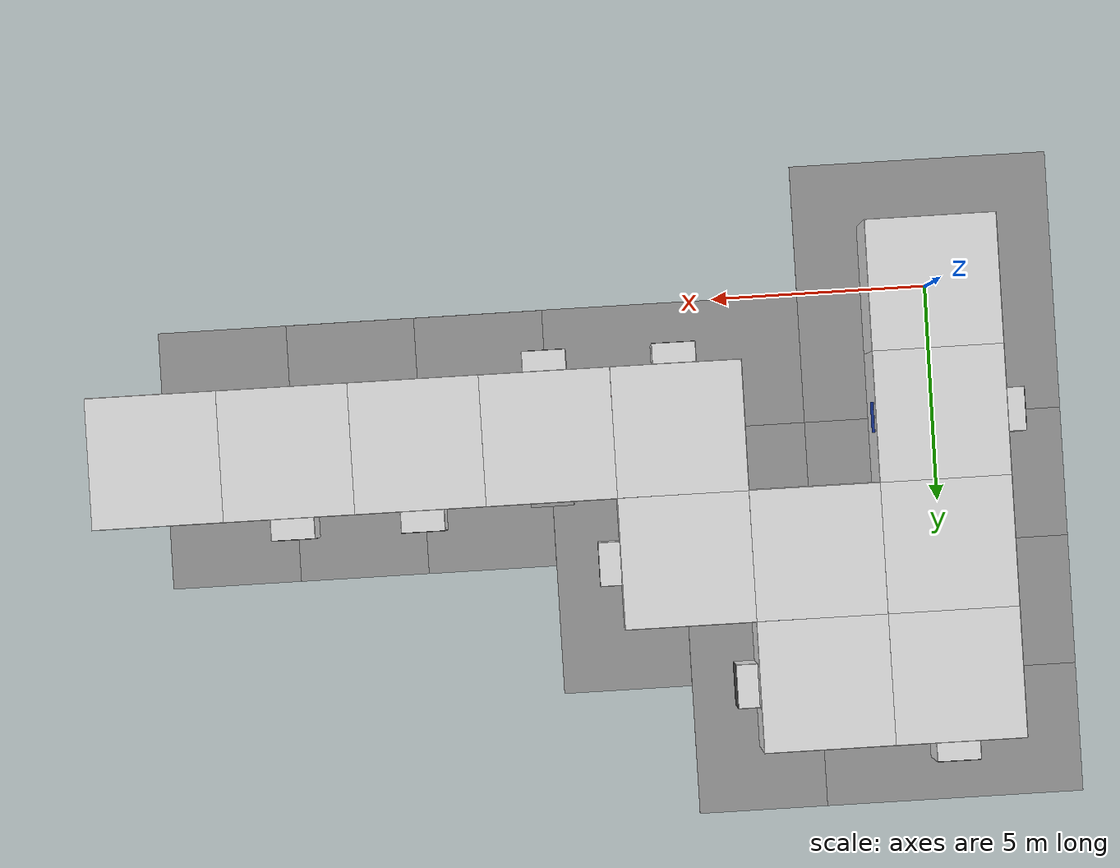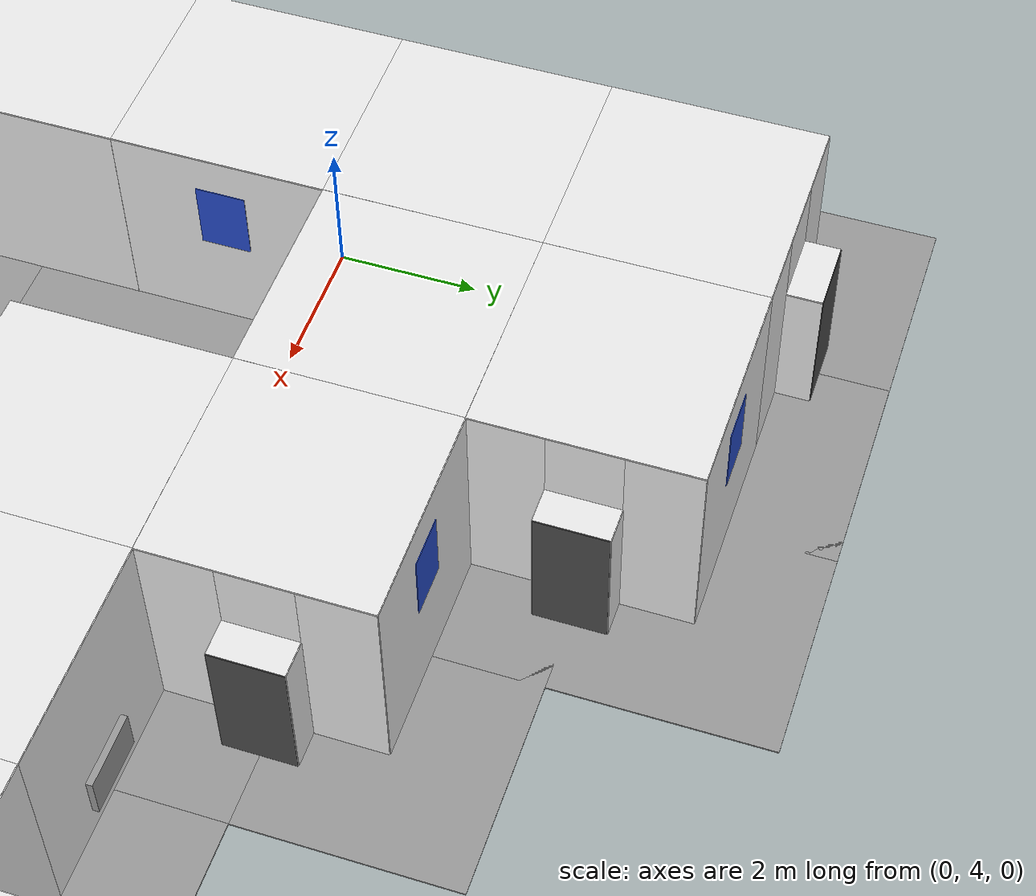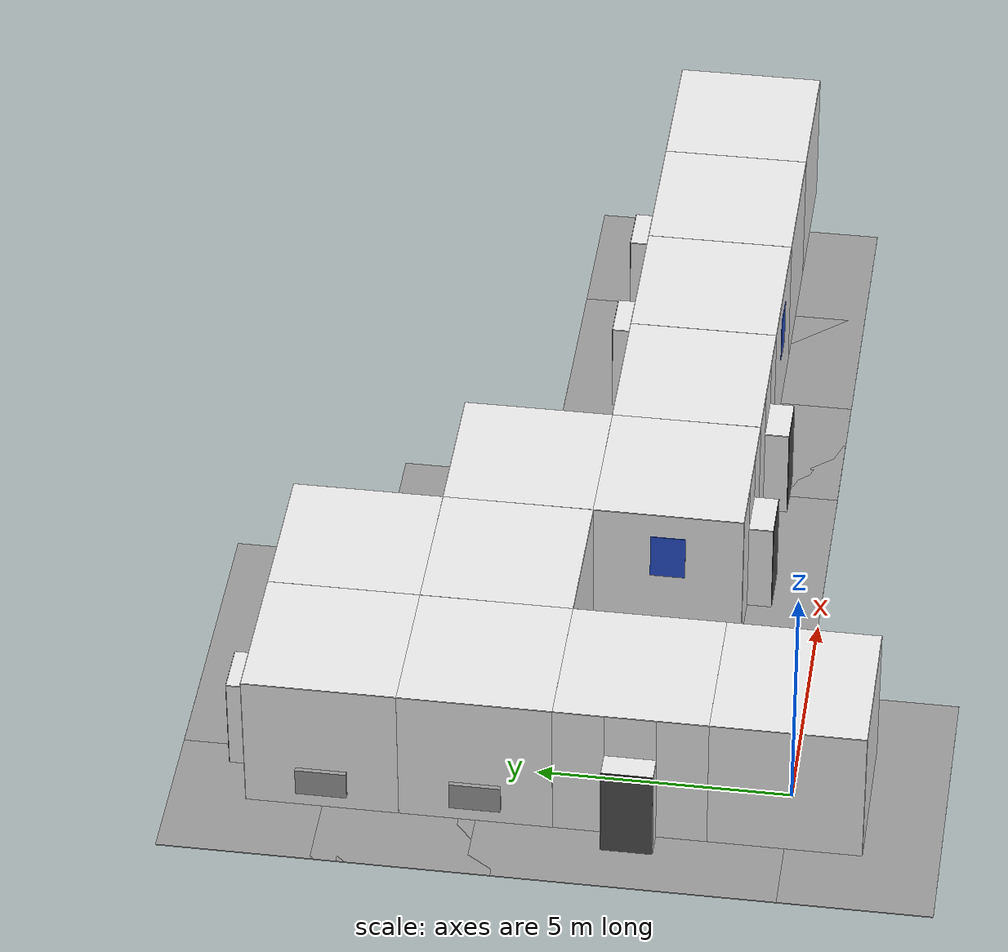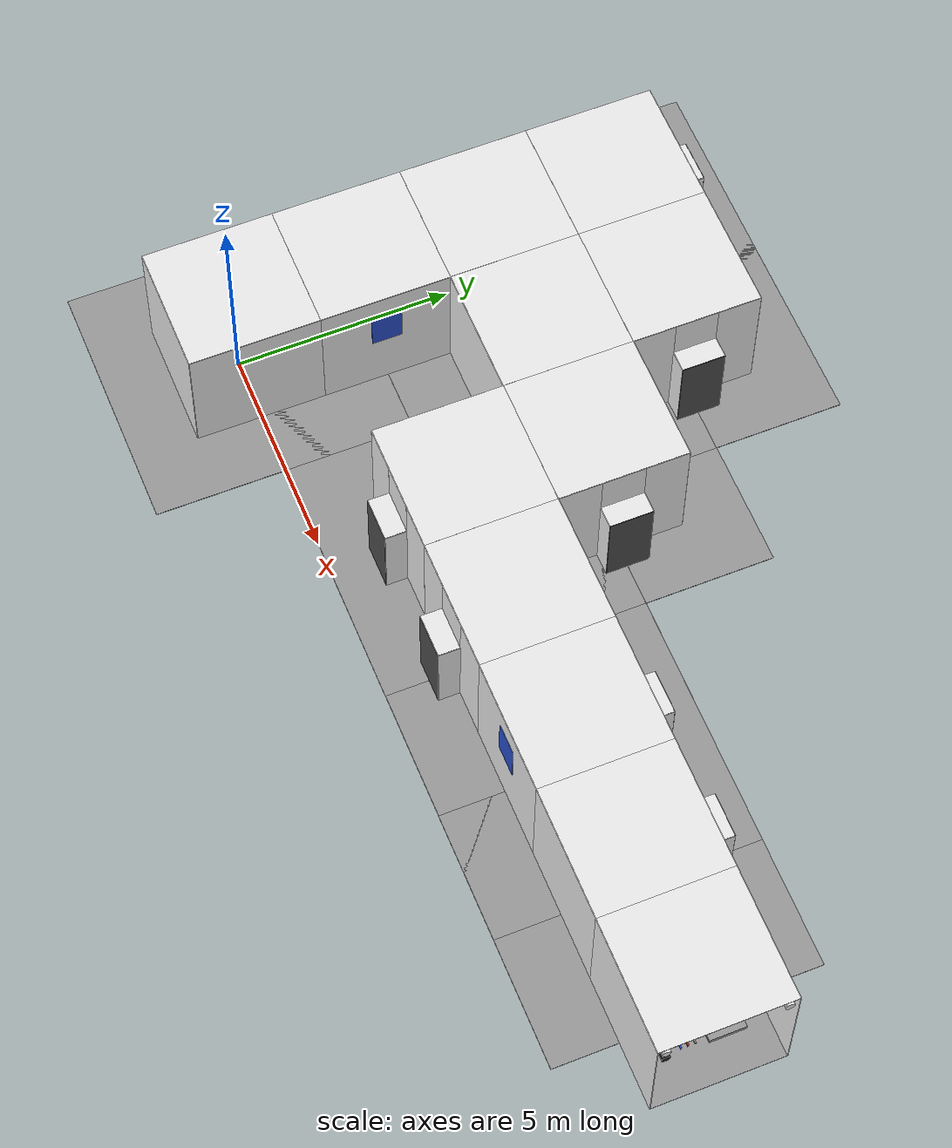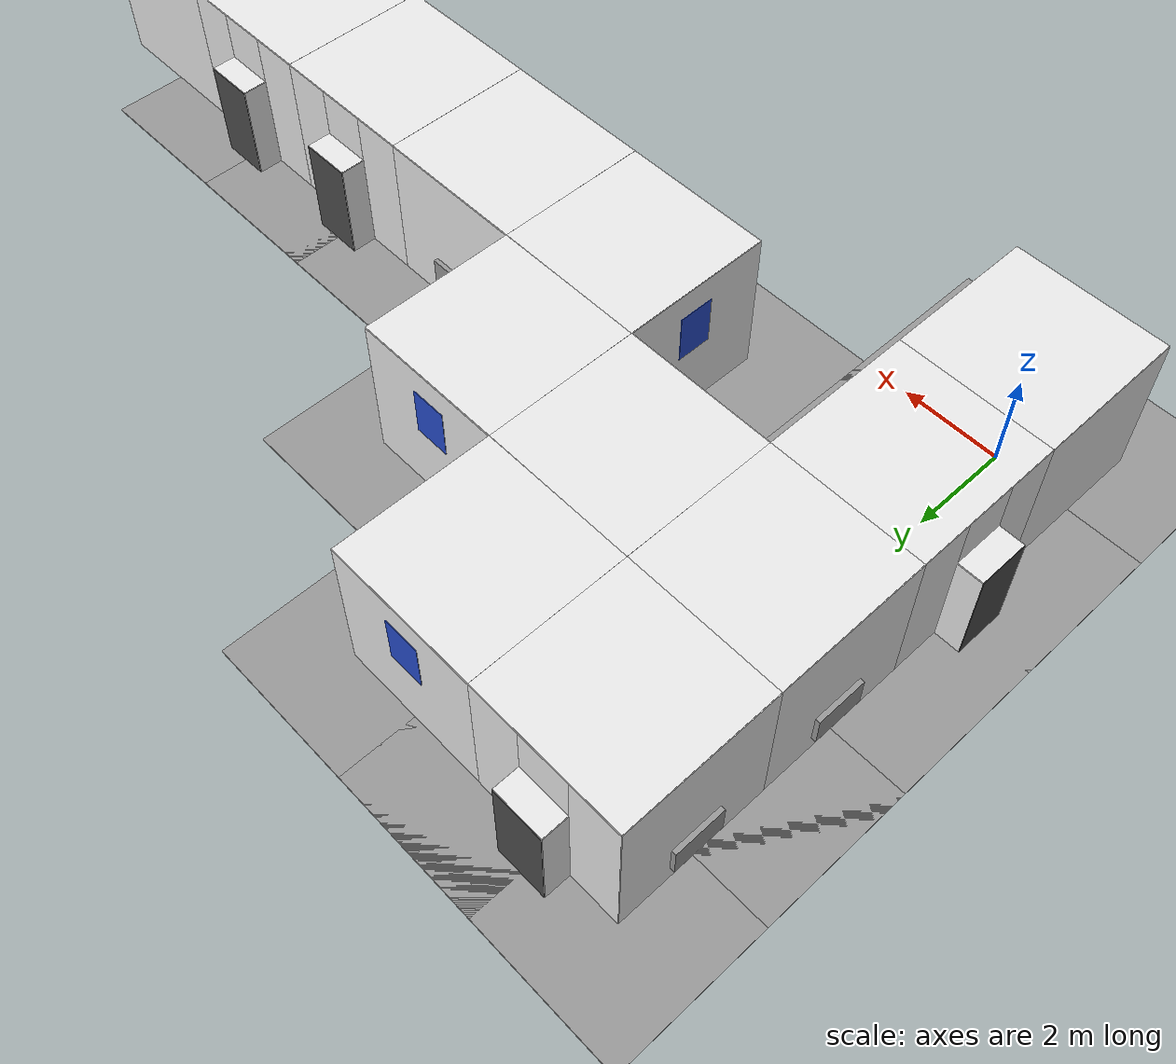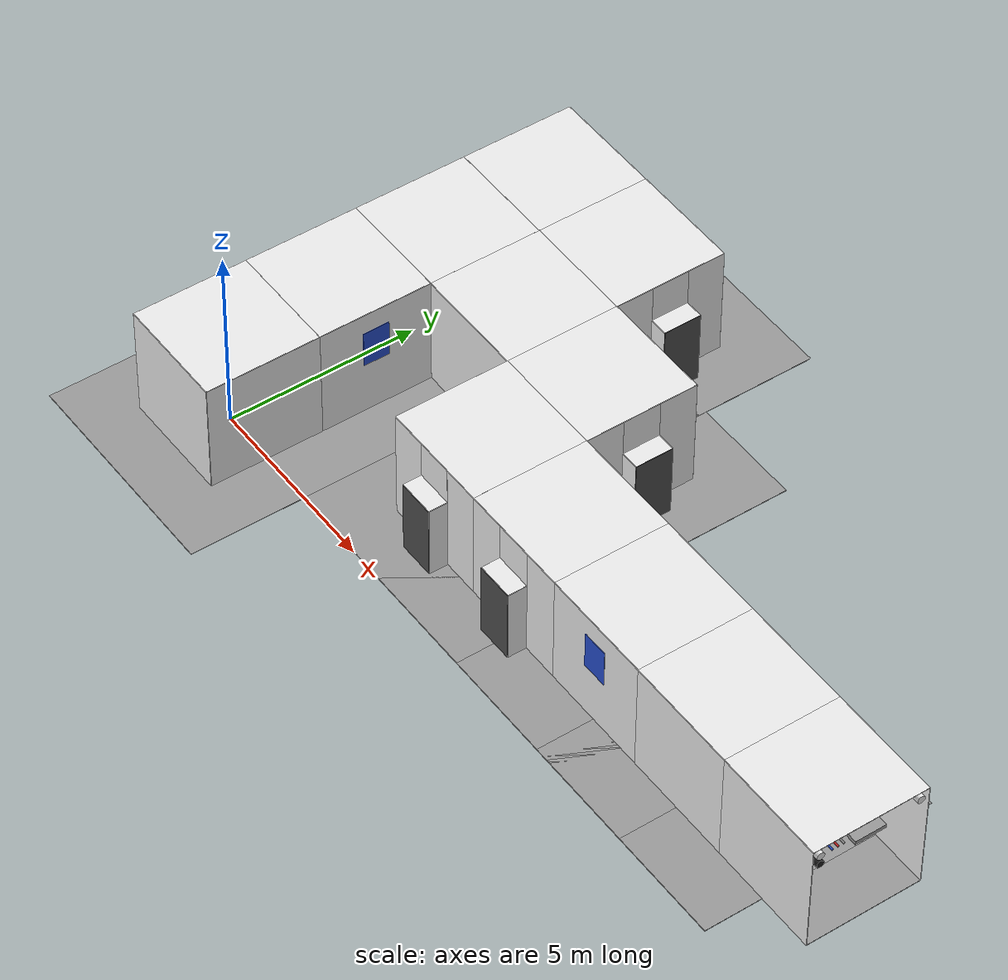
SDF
<sdf version="1.6">
 <world name="default">
  <gravity>0 0 -9.8</gravity>
  <magnetic_field>6e-06 2.3e-05 -4.2e-05</magnetic_field>
  <atmosphere type="adiabatic"/>
  <physics default="0" name="default_physics" type="ode">
   <max_step_size>0.001</max_step_size>
   <real_time_factor>1</real_time_factor>
   <real_time_update_rate>1000</real_time_update_rate>
  </physics>
  <scene><ambient>0.4 0.4 0.4 1</ambient><background>0.7 0.7 0.7 1</background><shadows>0</shadows></scene>
  <spherical_coordinates>
   <surface_model>EARTH_WGS84</surface_model>
   <latitude_deg>0</latitude_deg>
   <longitude_deg>0</longitude_deg>
   <elevation>0</elevation>
   <heading_deg>0</heading_deg>
  </spherical_coordinates>
  <model name="wall_back_0_0_0_0">
   <static>1</static>
   <pose>0.0 -1.5 1.5 0.0 0.0 0.0</pose>
   <link name="link">
    <collision name="collision"><geometry><box><size>3.0 0.02 3.0</size></box></geometry></collision>
    <visual name="visual">
     <material>
      <script><name>Gazebo/White</name><uri>file://media/materials/scripts/gazebo.material</uri></script>
     </material>
     <geometry><box><size>3.0 0.02 3.0</size></box></geometry>
    </visual>
   </link>
  </model>
  <model name="wall_right_0_0_0_0">
   <static>1</static>
   <pose>1.5 0.0 1.5 0.0 0.0 1.57</pose>
   <link name="link">
    <collision name="collision"><geometry><box><size>3.0 0.02 3.0</size></box></geometry></collision>
    <visual name="visual">
     <material>
      <script><name>Gazebo/White</name><uri>file://media/materials/scripts/gazebo.material</uri></script>
     </material>
     <geometry><box><size>3.0 0.02 3.0</size></box></geometry>
    </visual>
   </link>
  </model>
  <model name="wall_left_0_0_0_0">
   <static>1</static>
   <pose>-1.5 0.0 1.5 0.0 0.0 1.57</pose>
   <link name="link">
    <collision name="collision"><geometry><box><size>3.0 0.02 3.0</size></box></geometry></collision>
    <visual name="visual">
     <material>
      <script><name>Gazebo/White</name><uri>file://media/materials/scripts/gazebo.material</uri></script>
     </material>
     <geometry><box><size>3.0 0.02 3.0</size></box></geometry>
    </visual>
   </link>
  </model>
  <model name="wall_top_0_0_0_0">
   <static>1</static>
   <pose>0.0 0.0 3.0 1.57 0.0 0.0</pose>
   <link name="link">
    <collision name="collision"><geometry><box><size>3.0 0.02 3.0</size></box></geometry></collision>
    <visual name="visual">
     <material>
      <script><name>Gazebo/White</name><uri>file://media/materials/scripts/gazebo.material</uri></script>
     </material>
     <geometry><box><size>3.0 0.02 3.0</size></box></geometry>
    </visual>
   </link>
  </model>
  <light name="lightball_0_0_0_0_0" type="point">
   <cast_shadows>0</cast_shadows>
   <pose>-0.25 -0.25 2.99 0.0 0.0 0.0</pose>
   <diffuse>10 10 10 255</diffuse>
   <specular>10 10 10 255</specular>
  </light>
  <light name="lightball_1_0_0_0_0" type="point">
   <cast_shadows>0</cast_shadows>
   <pose>0.25 -0.25 2.99 0.0 0.0 0.0</pose>
   <diffuse>10 10 10 255</diffuse>
   <specular>10 10 10 255</specular>
  </light>
  <light name="lightball_2_0_0_0_0" type="point">
   <cast_shadows>0</cast_shadows>
   <pose>-0.25 0.25 2.99 0.0 0.0 0.0</pose>
   <diffuse>10 10 10 255</diffuse>
   <specular>10 10 10 255</specular>
  </light>
  <light name="lightball_3_0_0_0_0" type="point">
   <cast_shadows>0</cast_shadows>
   <pose>0.25 0.25 2.99 0.0 0.0 0.0</pose>
   <diffuse>10 10 10 255</diffuse>
   <specular>10 10 10 255</specular>
  </light>
  <model name="ceiling_1_0_0_0_0">
   <pose>0.0 0.0 2.55 0.0 0.0 0.0</pose>
   <link name="link_1">
    <visual name="visual">
     <geometry><box><size>0.8 1 0.1</size></box></geometry>
     <material>
      <script><uri>file://media/materials/scripts/gazebo.material</uri><name>Gazebo/Grey</name></script>
     </material>
    </visual>
    <collision name="collision"><geometry><box><size>0.8 1 0.1</size></box></geometry></collision>
   </link>
   <static>1</static>
  </model>
  <model name="ceiling_1_0_0_1_0">
   <pose>0.0 -1.0 2.55 0.0 0.0 0.0</pose>
   <link name="link_1">
    <visual name="visual">
     <geometry><box><size>0.8 1 0.1</size></box></geometry>
     <material>
      <script><uri>file://media/materials/scripts/gazebo.material</uri><name>Gazebo/Grey</name></script>
     </material>
    </visual>
    <collision name="collision"><geometry><box><size>0.8 1 0.1</size></box></geometry></collision>
   </link>
   <static>1</static>
  </model>
  <model name="ceiling_1_0_0_2_0">
   <pose>0.0 1.0 2.55 0.0 0.0 0.0</pose>
   <link name="link_1">
    <visual name="visual">
     <geometry><box><size>0.8 1 0.1</size></box></geometry>
     <material>
      <script><uri>file://media/materials/scripts/gazebo.material</uri><name>Gazebo/Grey</name></script>
     </material>
    </visual>
    <collision name="collision"><geometry><box><size>0.8 1 0.1</size></box></geometry></collision>
   </link>
   <static>1</static>
  </model>
  <model name="white_pipe_left_0_0_0_0">
   <static>1</static>
   <pose>0.0 0.0 2.76 0.0 0.0 0.0</pose>
   <link name="link_0">
    <visual name="visual">
     <pose>-1.3 0 0 1.57 0 0</pose>
     <geometry><cylinder><radius>0.1</radius><length>3.0</length></cylinder></geometry>
     <material>
      <script><uri>file://media/materials/scripts/gazebo.material</uri><name>Gazebo/White</name></script>
     </material>
    </visual>
    <collision name="collision">
     <pose>-1.3 0 0 1.57 0 0</pose>
     <geometry><cylinder><radius>0.1</radius><length>3.0</length></cylinder></geometry>
    </collision>
   </link>
  </model>
  <model name="white_pipe_right_0_0_0_0">
   <static>1</static>
   <pose>0.0 0.0 2.76 0.0 0.0 0.0</pose>
   <link name="link_0">
    <visual name="visual">
     <pose>1.3 0 0 1.57 0 0</pose>
     <geometry><cylinder><radius>0.1</radius><length>3.0</length></cylinder></geometry>
     <material>
      <script><uri>file://media/materials/scripts/gazebo.material</uri><name>Gazebo/White</name></script>
     </material>
    </visual>
    <collision name="collision">
     <pose>1.3 0 0 1.57 0 0</pose>
     <geometry><cylinder><radius>0.1</radius><length>3.0</length></cylinder></geometry>
    </collision>
   </link>
  </model>
  <model name="black_pipe_right_0_0_0_0">
   <static>1</static>
   <pose>0.0 0.0 2.76 0.0 0.0 0.0</pose>
   <link name="link_0">
    <visual name="visual">
     <pose>1.3 0 -0.25 1.57 0 0</pose>
     <geometry><cylinder><radius>0.1</radius><length>3.0</length></cylinder></geometry>
     <material>
      <script><uri>file://media/materials/scripts/gazebo.material</uri><name>Gazebo/Black</name></script>
     </material>
    </visual>
    <collision name="collision">
     <pose>1.3 0 -0.25 1.57 0 0</pose>
     <geometry><cylinder><radius>0.1</radius><length>3.0</length></cylinder></geometry>
    </collision>
   </link>
  </model>
  <model name="grey_pipe_right_0_0_0_0">
   <static>1</static>
   <pose>0.0 0.0 2.76 0.0 0.0 0.0</pose>
   <link name="link_0">
    <visual name="visual">
     <pose>0.7 0 0 1.57 0 0</pose>
     <geometry><cylinder><radius>0.02</radius><length>3.0</length></cylinder></geometry>
     <material>
      <script><uri>file://media/materials/scripts/gazebo.material</uri><name>Gazebo/Grey</name></script>
     </material>
    </visual>
    <collision name="collision">
     <pose>0.7 0 0 1.57 0 0</pose>
     <geometry><cylinder><radius>0.02</radius><length>3.0</length></cylinder></geometry>
    </collision>
   </link>
  </model>
  <model name="red_pipe_right_0_0_0_0">
   <static>1</static>
   <pose>0.0 0.0 2.76 0.0 0.0 0.0</pose>
   <link name="link_0">
    <visual name="visual">
     <pose>0.85 0 0 1.57 0 0</pose>
     <geometry><cylinder><radius>0.02</radius><length>3.0</length></cylinder></geometry>
     <material>
      <script><uri>file://media/materials/scripts/gazebo.material</uri><name>Gazebo/Red</name></script>
     </material>
    </visual>
    <collision name="collision">
     <pose>0.85 0 0 1.57 0 0</pose>
     <geometry><cylinder><radius>0.02</radius><length>3.0</length></cylinder></geometry>
    </collision>
   </link>
  </model>
  <model name="blue_pipe_right_0_0_0_0">
   <static>1</static>
   <pose>0.0 0.0 2.76 0.0 0.0 0.0</pose>
   <link name="link_0">
    <visual name="visual">
     <pose>1 0 0 1.57 0 0</pose>
     <geometry><cylinder><radius>0.02</radius><length>3.0</length></cylinder></geometry>
     <material>
      <script><uri>file://media/materials/scripts/gazebo.material</uri><name>Gazebo/Blue</name></script>
     </material>
    </visual>
    <collision name="collision">
     <pose>1 0 0 1.57 0 0</pose>
     <geometry><cylinder><radius>0.02</radius><length>3.0</length></cylinder></geometry>
    </collision>
   </link>
  </model>
  <model name="wall_bottom_0_0_0_0">
   <static>1</static>
   <link name="link">
    <collision name="collision"><geometry><box><size>6.0 6.0 0.02</size></box></geometry></collision>
    <visual name="visual">
     <material>
      <script><name>Gazebo/Grey</name><uri>file://media/materials/scripts/gazebo.material</uri></script>
     </material>
     <geometry><box><size>6.0 6.0 0.02</size></box></geometry>
    </visual>
   </link>
  </model>
  <model name="wall_right_0_1_0_1">
   <static>1</static>
   <pose>1.5 3.0 1.5 0.0 0.0 1.57</pose>
   <link name="link">
    <collision name="collision"><geometry><box><size>3.0 0.02 3.0</size></box></geometry></collision>
    <visual name="visual">
     <material>
      <script><name>Gazebo/White</name><uri>file://media/materials/scripts/gazebo.material</uri></script>
     </material>
     <geometry><box><size>3.0 0.02 3.0</size></box></geometry>
    </visual>
   </link>
  </model>
  <model name="wall_top_0_1_0_1">
   <static>1</static>
   <pose>0.0 3.0 3.0 1.57 0.0 0.0</pose>
   <link name="link">
    <collision name="collision"><geometry><box><size>3.0 0.02 3.0</size></box></geometry></collision>
    <visual name="visual">
     <material>
      <script><name>Gazebo/White</name><uri>file://media/materials/scripts/gazebo.material</uri></script>
     </material>
     <geometry><box><size>3.0 0.02 3.0</size></box></geometry>
    </visual>
   </link>
  </model>
  <light name="lightball_0_0_1_0_1" type="point">
   <cast_shadows>0</cast_shadows>
   <pose>-0.25 2.75 2.99 0.0 0.0 0.0</pose>
   <diffuse>10 10 10 255</diffuse>
   <specular>10 10 10 255</specular>
  </light>
  <light name="lightball_1_0_1_0_1" type="point">
   <cast_shadows>0</cast_shadows>
   <pose>0.25 2.75 2.99 0.0 0.0 0.0</pose>
   <diffuse>10 10 10 255</diffuse>
   <specular>10 10 10 255</specular>
  </light>
  <light name="lightball_2_0_1_0_1" type="point">
   <cast_shadows>0</cast_shadows>
   <pose>-0.25 3.25 2.99 0.0 0.0 0.0</pose>
   <diffuse>10 10 10 255</diffuse>
   <specular>10 10 10 255</specular>
  </light>
  <light name="lightball_3_0_1_0_1" type="point">
   <cast_shadows>0</cast_shadows>
   <pose>0.25 3.25 2.99 0.0 0.0 0.0</pose>
   <diffuse>10 10 10 255</diffuse>
   <specular>10 10 10 255</specular>
  </light>
  <model name="ceiling_1_0_1_0_1">
   <pose>0.0 3.0 2.55 0.0 0.0 0.0</pose>
   <link name="link_1">
    <visual name="visual">
     <geometry><box><size>0.8 1 0.1</size></box></geometry>
     <material>
      <script><uri>file://media/materials/scripts/gazebo.material</uri><name>Gazebo/Grey</name></script>
     </material>
    </visual>
    <collision name="collision"><geometry><box><size>0.8 1 0.1</size></box></geometry></collision>
   </link>
   <static>1</static>
  </model>
  <model name="ceiling_1_0_1_1_1">
   <pose>0.0 2.0 2.55 0.0 0.0 0.0</pose>
   <link name="link_1">
    <visual name="visual">
     <geometry><box><size>0.8 1 0.1</size></box></geometry>
     <material>
      <script><uri>file://media/materials/scripts/gazebo.material</uri><name>Gazebo/Grey</name></script>
     </material>
    </visual>
    <collision name="collision"><geometry><box><size>0.8 1 0.1</size></box></geometry></collision>
   </link>
   <static>1</static>
  </model>
  <model name="ceiling_1_0_1_2_1">
   <pose>0.0 4.0 2.55 0.0 0.0 0.0</pose>
   <link name="link_1">
    <visual name="visual">
     <geometry><box><size>0.8 1 0.1</size></box></geometry>
     <material>
      <script><uri>file://media/materials/scripts/gazebo.material</uri><name>Gazebo/Grey</name></script>
     </material>
    </visual>
    <collision name="collision"><geometry><box><size>0.8 1 0.1</size></box></geometry></collision>
   </link>
   <static>1</static>
  </model>
  <model name="white_pipe_left_0_1_0_1">
   <static>1</static>
   <pose>0.0 3.0 2.76 0.0 0.0 0.0</pose>
   <link name="link_0">
    <visual name="visual">
     <pose>-1.3 0 0 1.57 0 0</pose>
     <geometry><cylinder><radius>0.1</radius><length>3.0</length></cylinder></geometry>
     <material>
      <script><uri>file://media/materials/scripts/gazebo.material</uri><name>Gazebo/White</name></script>
     </material>
    </visual>
    <collision name="collision">
     <pose>-1.3 0 0 1.57 0 0</pose>
     <geometry><cylinder><radius>0.1</radius><length>3.0</length></cylinder></geometry>
    </collision>
   </link>
  </model>
  <model name="white_pipe_right_0_1_0_1">
   <static>1</static>
   <pose>0.0 3.0 2.76 0.0 0.0 0.0</pose>
   <link name="link_0">
    <visual name="visual">
     <pose>1.3 0 0 1.57 0 0</pose>
     <geometry><cylinder><radius>0.1</radius><length>3.0</length></cylinder></geometry>
     <material>
      <script><uri>file://media/materials/scripts/gazebo.material</uri><name>Gazebo/White</name></script>
     </material>
    </visual>
    <collision name="collision">
     <pose>1.3 0 0 1.57 0 0</pose>
     <geometry><cylinder><radius>0.1</radius><length>3.0</length></cylinder></geometry>
    </collision>
   </link>
  </model>
  <model name="black_pipe_right_0_1_0_1">
   <static>1</static>
   <pose>0.0 3.0 2.76 0.0 0.0 0.0</pose>
   <link name="link_0">
    <visual name="visual">
     <pose>1.3 0 -0.25 1.57 0 0</pose>
     <geometry><cylinder><radius>0.1</radius><length>3.0</length></cylinder></geometry>
     <material>
      <script><uri>file://media/materials/scripts/gazebo.material</uri><name>Gazebo/Black</name></script>
     </material>
    </visual>
    <collision name="collision">
     <pose>1.3 0 -0.25 1.57 0 0</pose>
     <geometry><cylinder><radius>0.1</radius><length>3.0</length></cylinder></geometry>
    </collision>
   </link>
  </model>
  <model name="grey_pipe_right_0_1_0_1">
   <static>1</static>
   <pose>0.0 3.0 2.76 0.0 0.0 0.0</pose>
   <link name="link_0">
    <visual name="visual">
     <pose>0.7 0 0 1.57 0 0</pose>
     <geometry><cylinder><radius>0.02</radius><length>3.0</length></cylinder></geometry>
     <material>
      <script><uri>file://media/materials/scripts/gazebo.material</uri><name>Gazebo/Grey</name></script>
     </material>
    </visual>
    <collision name="collision">
     <pose>0.7 0 0 1.57 0 0</pose>
     <geometry><cylinder><radius>0.02</radius><length>3.0</length></cylinder></geometry>
    </collision>
   </link>
  </model>
  <model name="red_pipe_right_0_1_0_1">
   <static>1</static>
   <pose>0.0 3.0 2.76 0.0 0.0 0.0</pose>
   <link name="link_0">
    <visual name="visual">
     <pose>0.85 0 0 1.57 0 0</pose>
     <geometry><cylinder><radius>0.02</radius><length>3.0</length></cylinder></geometry>
     <material>
      <script><uri>file://media/materials/scripts/gazebo.material</uri><name>Gazebo/Red</name></script>
     </material>
    </visual>
    <collision name="collision">
     <pose>0.85 0 0 1.57 0 0</pose>
     <geometry><cylinder><radius>0.02</radius><length>3.0</length></cylinder></geometry>
    </collision>
   </link>
  </model>
  <model name="blue_pipe_right_0_1_0_1">
   <static>1</static>
   <pose>0.0 3.0 2.76 0.0 0.0 0.0</pose>
   <link name="link_0">
    <visual name="visual">
     <pose>1 0 0 1.57 0 0</pose>
     <geometry><cylinder><radius>0.02</radius><length>3.0</length></cylinder></geometry>
     <material>
      <script><uri>file://media/materials/scripts/gazebo.material</uri><name>Gazebo/Blue</name></script>
     </material>
    </visual>
    <collision name="collision">
     <pose>1 0 0 1.57 0 0</pose>
     <geometry><cylinder><radius>0.02</radius><length>3.0</length></cylinder></geometry>
    </collision>
   </link>
  </model>
  <model name="panel_0_1_0_1">
   <static>1</static>
   <pose>1.5 3.0 1.95 0.0 0.0 0.0</pose>
   <link name="link">
    <collision name="collision"><geometry><box><size>0.04 0.7 1</size></box></geometry></collision>
    <visual name="visual">
     <material>
      <script><name>Gazebo/Blue</name><uri>file://media/materials/scripts/gazebo.material</uri></script>
     </material>
     <geometry><box><size>0.04 0.7 1</size></box></geometry>
    </visual>
   </link>
  </model>
  <model name="wall_left_front_left_0_1_0_1">
   <static>1</static>
   <pose>-1.5 4.0 1.5 0.0 0.0 1.57</pose>
   <link name="link">
    <collision name="collision"><geometry><box><size>1.0 0.02 3.0</size></box></geometry></collision>
    <visual name="visual">
     <material>
      <script><name>Gazebo/White</name><uri>file://media/materials/scripts/gazebo.material</uri></script>
     </material>
     <geometry><box><size>1.0 0.02 3.0</size></box></geometry>
    </visual>
   </link>
  </model>
  <model name="wall_left_front_right_0_1_0_1">
   <static>1</static>
   <pose>-1.5 2.0 1.5 0.0 0.0 1.57</pose>
   <link name="link">
    <collision name="collision"><geometry><box><size>1.0 0.02 3.0</size></box></geometry></collision>
    <visual name="visual">
     <material>
      <script><name>Gazebo/White</name><uri>file://media/materials/scripts/gazebo.material</uri></script>
     </material>
     <geometry><box><size>1.0 0.02 3.0</size></box></geometry>
    </visual>
   </link>
  </model>
  <model name="wall_left_front_up_0_1_0_1">
   <static>1</static>
   <pose>-1.5 3.0 2.5 0.0 0.0 1.57</pose>
   <link name="link">
    <collision name="collision"><geometry><box><size>1.0 0.02 1.0</size></box></geometry></collision>
    <visual name="visual">
     <material>
      <script><name>Gazebo/White</name><uri>file://media/materials/scripts/gazebo.material</uri></script>
     </material>
     <geometry><box><size>1.0 0.02 1.0</size></box></geometry>
    </visual>
   </link>
  </model>
  <model name="wall_left_inside_back_0_1_0_1">
   <static>1</static>
   <pose>-2.0 3.0 1.0 0.0 0.0 1.57</pose>
   <link name="link">
    <collision name="collision"><geometry><box><size>1 0.02 2</size></box></geometry></collision>
    <visual name="visual">
     <material>
      <script><name>Gazebo/DarkGrey</name><uri>file://media/materials/scripts/gazebo.material</uri></script>
     </material>
     <geometry><box><size>1 0.02 2</size></box></geometry>
    </visual>
   </link>
  </model>
  <model name="wall_left_inside_left_0_1_0_1">
   <static>1</static>
   <pose>-1.75 3.5 1.0 0.0 0.0 0.0</pose>
   <link name="link">
    <collision name="collision"><geometry><box><size>0.5 0.02 2</size></box></geometry></collision>
    <visual name="visual">
     <material>
      <script><name>Gazebo/White</name><uri>file://media/materials/scripts/gazebo.material</uri></script>
     </material>
     <geometry><box><size>0.5 0.02 2</size></box></geometry>
    </visual>
   </link>
  </model>
  <model name="wall_left_inside_right_0_1_0_1">
   <static>1</static>
   <pose>-1.75 2.5 1.0 0.0 0.0 0.0</pose>
   <link name="link">
    <collision name="collision"><geometry><box><size>0.5 0.02 2</size></box></geometry></collision>
    <visual name="visual">
     <material>
      <script><name>Gazebo/White</name><uri>file://media/materials/scripts/gazebo.material</uri></script>
     </material>
     <geometry><box><size>0.5 0.02 2</size></box></geometry>
    </visual>
   </link>
  </model>
  <model name="wall_left_inside_top_0_1_0_1">
   <static>1</static>
   <pose>-1.75 3.0 2.0 1.57 0.0 1.57</pose>
   <link name="link">
    <collision name="collision"><geometry><box><size>1 0.02 0.5</size></box></geometry></collision>
    <visual name="visual">
     <material>
      <script><name>Gazebo/White</name><uri>file://media/materials/scripts/gazebo.material</uri></script>
     </material>
     <geometry><box><size>1 0.02 0.5</size></box></geometry>
    </visual>
   </link>
  </model>
  <model name="wall_bottom_0_1_0_1">
   <static>1</static>
   <pose>0.0 3.0 0.0 0.0 0.0 0.0</pose>
   <link name="link">
    <collision name="collision"><geometry><box><size>6.0 6.0 0.02</size></box></geometry></collision>
    <visual name="visual">
     <material>
      <script><name>Gazebo/Grey</name><uri>file://media/materials/scripts/gazebo.material</uri></script>
     </material>
     <geometry><box><size>6.0 6.0 0.02</size></box></geometry>
    </visual>
   </link>
  </model>
  <model name="wall_right_0_2_0_1">
   <static>1</static>
   <pose>1.5 6.0 1.5 0.0 0.0 1.57</pose>
   <link name="link">
    <collision name="collision"><geometry><box><size>3.0 0.02 3.0</size></box></geometry></collision>
    <visual name="visual">
     <material>
      <script><name>Gazebo/White</name><uri>file://media/materials/scripts/gazebo.material</uri></script>
     </material>
     <geometry><box><size>3.0 0.02 3.0</size></box></geometry>
    </visual>
   </link>
  </model>
  <model name="wall_left_0_2_0_1">
   <static>1</static>
   <pose>-1.5 6.0 1.5 0.0 0.0 1.57</pose>
   <link name="link">
    <collision name="collision"><geometry><box><size>3.0 0.02 3.0</size></box></geometry></collision>
    <visual name="visual">
     <material>
      <script><name>Gazebo/White</name><uri>file://media/materials/scripts/gazebo.material</uri></script>
     </material>
     <geometry><box><size>3.0 0.02 3.0</size></box></geometry>
    </visual>
   </link>
  </model>
  <model name="wall_top_0_2_0_1">
   <static>1</static>
   <pose>0.0 6.0 3.0 1.57 0.0 0.0</pose>
   <link name="link">
    <collision name="collision"><geometry><box><size>3.0 0.02 3.0</size></box></geometry></collision>
    <visual name="visual">
     <material>
      <script><name>Gazebo/White</name><uri>file://media/materials/scripts/gazebo.material</uri></script>
     </material>
     <geometry><box><size>3.0 0.02 3.0</size></box></geometry>
    </visual>
   </link>
  </model>
  <light name="lightball_0_0_2_0_1" type="point">
   <cast_shadows>0</cast_shadows>
   <pose>-0.25 5.75 2.99 0.0 0.0 0.0</pose>
   <diffuse>10 10 10 255</diffuse>
   <specular>10 10 10 255</specular>
  </light>
  <light name="lightball_1_0_2_0_1" type="point">
   <cast_shadows>0</cast_shadows>
   <pose>0.25 5.75 2.99 0.0 0.0 0.0</pose>
   <diffuse>10 10 10 255</diffuse>
   <specular>10 10 10 255</specular>
  </light>
  <light name="lightball_2_0_2_0_1" type="point">
   <cast_shadows>0</cast_shadows>
   <pose>-0.25 6.25 2.99 0.0 0.0 0.0</pose>
   <diffuse>10 10 10 255</diffuse>
   <specular>10 10 10 255</specular>
  </light>
  <light name="lightball_3_0_2_0_1" type="point">
   <cast_shadows>0</cast_shadows>
   <pose>0.25 6.25 2.99 0.0 0.0 0.0</pose>
   <diffuse>10 10 10 255</diffuse>
   <specular>10 10 10 255</specular>
  </light>
  <model name="ceiling_1_0_2_0_1">
   <pose>0.0 6.0 2.55 0.0 0.0 0.0</pose>
   <link name="link_1">
    <visual name="visual">
     <geometry><box><size>0.8 1 0.1</size></box></geometry>
     <material>
      <script><uri>file://media/materials/scripts/gazebo.material</uri><name>Gazebo/Grey</name></script>
     </material>
    </visual>
    <collision name="collision"><geometry><box><size>0.8 1 0.1</size></box></geometry></collision>
   </link>
   <static>1</static>
  </model>
  <model name="ceiling_1_0_2_1_1">
   <pose>0.0 5.0 2.55 0.0 0.0 0.0</pose>
   <link name="link_1">
    <visual name="visual">
     <geometry><box><size>0.8 1 0.1</size></box></geometry>
     <material>
      <script><uri>file://media/materials/scripts/gazebo.material</uri><name>Gazebo/Grey</name></script>
     </material>
    </visual>
    <collision name="collision"><geometry><box><size>0.8 1 0.1</size></box></geometry></collision>
   </link>
   <static>1</static>
  </model>
  <model name="ceiling_1_0_2_2_1">
   <pose>0.0 7.0 2.55 0.0 0.0 0.0</pose>
   <link name="link_1">
    <visual name="visual">
     <geometry><box><size>0.8 1 0.1</size></box></geometry>
     <material>
      <script><uri>file://media/materials/scripts/gazebo.material</uri><name>Gazebo/Grey</name></script>
     </material>
    </visual>
    <collision name="collision"><geometry><box><size>0.8 1 0.1</size></box></geometry></collision>
   </link>
   <static>1</static>
  </model>
  <model name="white_pipe_left_0_2_0_1">
   <static>1</static>
   <pose>0.0 6.0 2.76 0.0 0.0 0.0</pose>
   <link name="link_0">
    <visual name="visual">
     <pose>-1.3 0 0 1.57 0 0</pose>
     <geometry><cylinder><radius>0.1</radius><length>3.0</length></cylinder></geometry>
     <material>
      <script><uri>file://media/materials/scripts/gazebo.material</uri><name>Gazebo/White</name></script>
     </material>
    </visual>
    <collision name="collision">
     <pose>-1.3 0 0 1.57 0 0</pose>
     <geometry><cylinder><radius>0.1</radius><length>3.0</length></cylinder></geometry>
    </collision>
   </link>
  </model>
  <model name="white_pipe_right_0_2_0_1">
   <static>1</static>
   <pose>0.0 6.0 2.76 0.0 0.0 0.0</pose>
   <link name="link_0">
    <visual name="visual">
     <pose>1.3 0 0 1.57 0 0</pose>
     <geometry><cylinder><radius>0.1</radius><length>3.0</length></cylinder></geometry>
     <material>
      <script><uri>file://media/materials/scripts/gazebo.material</uri><name>Gazebo/White</name></script>
     </material>
    </visual>
    <collision name="collision">
     <pose>1.3 0 0 1.57 0 0</pose>
     <geometry><cylinder><radius>0.1</radius><length>3.0</length></cylinder></geometry>
    </collision>
   </link>
  </model>
  <model name="black_pipe_right_0_2_0_1">
   <static>1</static>
   <pose>0.0 6.0 2.76 0.0 0.0 0.0</pose>
   <link name="link_0">
    <visual name="visual">
     <pose>1.3 0 -0.25 1.57 0 0</pose>
     <geometry><cylinder><radius>0.1</radius><length>3.0</length></cylinder></geometry>
     <material>
      <script><uri>file://media/materials/scripts/gazebo.material</uri><name>Gazebo/Black</name></script>
     </material>
    </visual>
    <collision name="collision">
     <pose>1.3 0 -0.25 1.57 0 0</pose>
     <geometry><cylinder><radius>0.1</radius><length>3.0</length></cylinder></geometry>
    </collision>
   </link>
  </model>
  <model name="grey_pipe_right_0_2_0_1">
   <static>1</static>
   <pose>0.0 6.0 2.76 0.0 0.0 0.0</pose>
   <link name="link_0">
    <visual name="visual">
     <pose>0.7 0 0 1.57 0 0</pose>
     <geometry><cylinder><radius>0.02</radius><length>3.0</length></cylinder></geometry>
     <material>
      <script><uri>file://media/materials/scripts/gazebo.material</uri><name>Gazebo/Grey</name></script>
     </material>
    </visual>
    <collision name="collision">
     <pose>0.7 0 0 1.57 0 0</pose>
     <geometry><cylinder><radius>0.02</radius><length>3.0</length></cylinder></geometry>
    </collision>
   </link>
  </model>
  <model name="red_pipe_right_0_2_0_1">
   <static>1</static>
   <pose>0.0 6.0 2.76 0.0 0.0 0.0</pose>
   <link name="link_0">
    <visual name="visual">
     <pose>0.85 0 0 1.57 0 0</pose>
     <geometry><cylinder><radius>0.02</radius><length>3.0</length></cylinder></geometry>
     <material>
      <script><uri>file://media/materials/scripts/gazebo.material</uri><name>Gazebo/Red</name></script>
     </material>
    </visual>
    <collision name="collision">
     <pose>0.85 0 0 1.57 0 0</pose>
     <geometry><cylinder><radius>0.02</radius><length>3.0</length></cylinder></geometry>
    </collision>
   </link>
  </model>
  <model name="blue_pipe_right_0_2_0_1">
   <static>1</static>
   <pose>0.0 6.0 2.76 0.0 0.0 0.0</pose>
   <link name="link_0">
    <visual name="visual">
     <pose>1 0 0 1.57 0 0</pose>
     <geometry><cylinder><radius>0.02</radius><length>3.0</length></cylinder></geometry>
     <material>
      <script><uri>file://media/materials/scripts/gazebo.material</uri><name>Gazebo/Blue</name></script>
     </material>
    </visual>
    <collision name="collision">
     <pose>1 0 0 1.57 0 0</pose>
     <geometry><cylinder><radius>0.02</radius><length>3.0</length></cylinder></geometry>
    </collision>
   </link>
  </model>
  <model name="wall_bottom_0_2_0_1">
   <static>1</static>
   <pose>0.0 6.0 0.0 0.0 0.0 0.0</pose>
   <link name="link">
    <collision name="collision"><geometry><box><size>6.0 6.0 0.02</size></box></geometry></collision>
    <visual name="visual">
     <material>
      <script><name>Gazebo/Grey</name><uri>file://media/materials/scripts/gazebo.material</uri></script>
     </material>
     <geometry><box><size>6.0 6.0 0.02</size></box></geometry>
    </visual>
   </link>
  </model>
  <model name="panel_0_2_0_1">
   <static>1</static>
   <pose>-1.5 6.0 0.66 0.0 0.0 0.0</pose>
   <link name="link">
    <collision name="collision"><geometry><box><size>0.2 1 0.6</size></box></geometry></collision>
    <visual name="visual">
     <material>
      <script><name>Gazebo/Grey</name><uri>file://media/materials/scripts/gazebo.material</uri></script>
     </material>
     <geometry><box><size>0.2 1 0.6</size></box></geometry>
    </visual>
   </link>
  </model>
  <model name="wall_left_0_3_0_2">
   <static>1</static>
   <pose>-1.5 9.0 1.5 0.0 0.0 1.57</pose>
   <link name="link">
    <collision name="collision"><geometry><box><size>3.0 0.02 3.0</size></box></geometry></collision>
    <visual name="visual">
     <material>
      <script><name>Gazebo/White</name><uri>file://media/materials/scripts/gazebo.material</uri></script>
     </material>
     <geometry><box><size>3.0 0.02 3.0</size></box></geometry>
    </visual>
   </link>
  </model>
  <model name="wall_top_0_3_0_2">
   <static>1</static>
   <pose>0.0 9.0 3.0 1.57 0.0 0.0</pose>
   <link name="link">
    <collision name="collision"><geometry><box><size>3.0 0.02 3.0</size></box></geometry></collision>
    <visual name="visual">
     <material>
      <script><name>Gazebo/White</name><uri>file://media/materials/scripts/gazebo.material</uri></script>
     </material>
     <geometry><box><size>3.0 0.02 3.0</size></box></geometry>
    </visual>
   </link>
  </model>
  <light name="lightball_0_0_3_0_2" type="point">
   <cast_shadows>0</cast_shadows>
   <pose>-0.25 8.75 2.99 0.0 0.0 0.0</pose>
   <diffuse>10 10 10 255</diffuse>
   <specular>10 10 10 255</specular>
  </light>
  <light name="lightball_1_0_3_0_2" type="point">
   <cast_shadows>0</cast_shadows>
   <pose>0.25 8.75 2.99 0.0 0.0 0.0</pose>
   <diffuse>10 10 10 255</diffuse>
   <specular>10 10 10 255</specular>
  </light>
  <light name="lightball_2_0_3_0_2" type="point">
   <cast_shadows>0</cast_shadows>
   <pose>-0.25 9.25 2.99 0.0 0.0 0.0</pose>
   <diffuse>10 10 10 255</diffuse>
   <specular>10 10 10 255</specular>
  </light>
  <light name="lightball_3_0_3_0_2" type="point">
   <cast_shadows>0</cast_shadows>
   <pose>0.25 9.25 2.99 0.0 0.0 0.0</pose>
   <diffuse>10 10 10 255</diffuse>
   <specular>10 10 10 255</specular>
  </light>
  <model name="ceiling_1_0_3_0_2">
   <pose>0.0 8.0 2.55 0.0 0.0 0.0</pose>
   <link name="link_1">
    <visual name="visual">
     <geometry><box><size>0.8 1 0.1</size></box></geometry>
     <material>
      <script><uri>file://media/materials/scripts/gazebo.material</uri><name>Gazebo/Grey</name></script>
     </material>
    </visual>
    <collision name="collision"><geometry><box><size>0.8 1 0.1</size></box></geometry></collision>
   </link>
   <static>1</static>
  </model>
  <model name="ceiling_1_0_3_1_2">
   <pose>1.0 9.0 2.55 0.0 0.0 1.57</pose>
   <link name="link_1">
    <visual name="visual">
     <geometry><box><size>0.8 1 0.1</size></box></geometry>
     <material>
      <script><uri>file://media/materials/scripts/gazebo.material</uri><name>Gazebo/Grey</name></script>
     </material>
    </visual>
    <collision name="collision"><geometry><box><size>0.8 1 0.1</size></box></geometry></collision>
   </link>
   <static>1</static>
  </model>
  <model name="white_pipe_left_0_3_0_2">
   <static>1</static>
   <pose>0.0 9.0 2.76 0.0 0.0 0.0</pose>
   <link name="link_0">
    <visual name="visual">
     <pose>-1.3 0 0 1.57 0 0</pose>
     <geometry><cylinder><radius>0.1</radius><length>3.0</length></cylinder></geometry>
     <material>
      <script><uri>file://media/materials/scripts/gazebo.material</uri><name>Gazebo/White</name></script>
     </material>
    </visual>
    <collision name="collision">
     <pose>-1.3 0 0 1.57 0 0</pose>
     <geometry><cylinder><radius>0.1</radius><length>3.0</length></cylinder></geometry>
    </collision>
   </link>
  </model>
  <model name="white_pipe_right_0_3_0_2">
   <static>1</static>
   <pose>0.0 9.0 2.76 0.0 0.0 0.0</pose>
   <link name="link_0">
    <visual name="visual">
     <pose>1.3 0 0 1.57 0 0</pose>
     <geometry><cylinder><radius>0.1</radius><length>3.0</length></cylinder></geometry>
     <material>
      <script><uri>file://media/materials/scripts/gazebo.material</uri><name>Gazebo/White</name></script>
     </material>
    </visual>
    <collision name="collision">
     <pose>1.3 0 0 1.57 0 0</pose>
     <geometry><cylinder><radius>0.1</radius><length>3.0</length></cylinder></geometry>
    </collision>
   </link>
  </model>
  <model name="black_pipe_right_0_3_0_2">
   <static>1</static>
   <pose>0.0 9.0 2.76 0.0 0.0 0.0</pose>
   <link name="link_0">
    <visual name="visual">
     <pose>1.3 0 -0.25 1.57 0 0</pose>
     <geometry><cylinder><radius>0.1</radius><length>3.0</length></cylinder></geometry>
     <material>
      <script><uri>file://media/materials/scripts/gazebo.material</uri><name>Gazebo/Black</name></script>
     </material>
    </visual>
    <collision name="collision">
     <pose>1.3 0 -0.25 1.57 0 0</pose>
     <geometry><cylinder><radius>0.1</radius><length>3.0</length></cylinder></geometry>
    </collision>
   </link>
  </model>
  <model name="grey_pipe_right_0_3_0_2">
   <static>1</static>
   <pose>0.0 9.0 2.76 0.0 0.0 0.0</pose>
   <link name="link_0">
    <visual name="visual">
     <pose>0.7 0 0 1.57 0 0</pose>
     <geometry><cylinder><radius>0.02</radius><length>3.0</length></cylinder></geometry>
     <material>
      <script><uri>file://media/materials/scripts/gazebo.material</uri><name>Gazebo/Grey</name></script>
     </material>
    </visual>
    <collision name="collision">
     <pose>0.7 0 0 1.57 0 0</pose>
     <geometry><cylinder><radius>0.02</radius><length>3.0</length></cylinder></geometry>
    </collision>
   </link>
  </model>
  <model name="red_pipe_right_0_3_0_2">
   <static>1</static>
   <pose>0.0 9.0 2.76 0.0 0.0 0.0</pose>
   <link name="link_0">
    <visual name="visual">
     <pose>0.85 0 0 1.57 0 0</pose>
     <geometry><cylinder><radius>0.02</radius><length>3.0</length></cylinder></geometry>
     <material>
      <script><uri>file://media/materials/scripts/gazebo.material</uri><name>Gazebo/Red</name></script>
     </material>
    </visual>
    <collision name="collision">
     <pose>0.85 0 0 1.57 0 0</pose>
     <geometry><cylinder><radius>0.02</radius><length>3.0</length></cylinder></geometry>
    </collision>
   </link>
  </model>
  <model name="blue_pipe_right_0_3_0_2">
   <static>1</static>
   <pose>0.0 9.0 2.76 0.0 0.0 0.0</pose>
   <link name="link_0">
    <visual name="visual">
     <pose>1 0 0 1.57 0 0</pose>
     <geometry><cylinder><radius>0.02</radius><length>3.0</length></cylinder></geometry>
     <material>
      <script><uri>file://media/materials/scripts/gazebo.material</uri><name>Gazebo/Blue</name></script>
     </material>
    </visual>
    <collision name="collision">
     <pose>1 0 0 1.57 0 0</pose>
     <geometry><cylinder><radius>0.02</radius><length>3.0</length></cylinder></geometry>
    </collision>
   </link>
  </model>
  <model name="white_pipe_left_1_0_3_0_2">
   <static>1</static>
   <pose>0.0 9.0 2.76 0.0 0.0 1.57</pose>
   <link name="link_0">
    <visual name="visual">
     <pose>-1.3 0 0 1.57 0 0</pose>
     <geometry><cylinder><radius>0.1</radius><length>3.0</length></cylinder></geometry>
     <material>
      <script><uri>file://media/materials/scripts/gazebo.material</uri><name>Gazebo/White</name></script>
     </material>
    </visual>
    <collision name="collision">
     <pose>-1.3 0 0 1.57 0 0</pose>
     <geometry><cylinder><radius>0.1</radius><length>3.0</length></cylinder></geometry>
    </collision>
   </link>
  </model>
  <model name="white_pipe_right_1_0_3_0_2">
   <static>1</static>
   <pose>0.0 9.0 2.76 0.0 0.0 1.57</pose>
   <link name="link_0">
    <visual name="visual">
     <pose>1.3 0 0 1.57 0 0</pose>
     <geometry><cylinder><radius>0.1</radius><length>3.0</length></cylinder></geometry>
     <material>
      <script><uri>file://media/materials/scripts/gazebo.material</uri><name>Gazebo/White</name></script>
     </material>
    </visual>
    <collision name="collision">
     <pose>1.3 0 0 1.57 0 0</pose>
     <geometry><cylinder><radius>0.1</radius><length>3.0</length></cylinder></geometry>
    </collision>
   </link>
  </model>
  <model name="black_pipe_right_1_0_3_0_2">
   <static>1</static>
   <pose>0.0 9.0 2.76 0.0 0.0 1.57</pose>
   <link name="link_0">
    <visual name="visual">
     <pose>1.3 0 -0.25 1.57 0 0</pose>
     <geometry><cylinder><radius>0.1</radius><length>3.0</length></cylinder></geometry>
     <material>
      <script><uri>file://media/materials/scripts/gazebo.material</uri><name>Gazebo/Black</name></script>
     </material>
    </visual>
    <collision name="collision">
     <pose>1.3 0 -0.25 1.57 0 0</pose>
     <geometry><cylinder><radius>0.1</radius><length>3.0</length></cylinder></geometry>
    </collision>
   </link>
  </model>
  <model name="grey_pipe_right_1_0_3_0_2">
   <static>1</static>
   <pose>0.0 9.0 2.76 0.0 0.0 1.57</pose>
   <link name="link_0">
    <visual name="visual">
     <pose>0.7 0 0 1.57 0 0</pose>
     <geometry><cylinder><radius>0.02</radius><length>3.0</length></cylinder></geometry>
     <material>
      <script><uri>file://media/materials/scripts/gazebo.material</uri><name>Gazebo/Grey</name></script>
     </material>
    </visual>
    <collision name="collision">
     <pose>0.7 0 0 1.57 0 0</pose>
     <geometry><cylinder><radius>0.02</radius><length>3.0</length></cylinder></geometry>
    </collision>
   </link>
  </model>
  <model name="red_pipe_right_1_0_3_0_2">
   <static>1</static>
   <pose>0.0 9.0 2.76 0.0 0.0 1.57</pose>
   <link name="link_0">
    <visual name="visual">
     <pose>0.85 0 0 1.57 0 0</pose>
     <geometry><cylinder><radius>0.02</radius><length>3.0</length></cylinder></geometry>
     <material>
      <script><uri>file://media/materials/scripts/gazebo.material</uri><name>Gazebo/Red</name></script>
     </material>
    </visual>
    <collision name="collision">
     <pose>0.85 0 0 1.57 0 0</pose>
     <geometry><cylinder><radius>0.02</radius><length>3.0</length></cylinder></geometry>
    </collision>
   </link>
  </model>
  <model name="blue_pipe_right_1_0_3_0_2">
   <static>1</static>
   <pose>0.0 9.0 2.76 0.0 0.0 1.57</pose>
   <link name="link_0">
    <visual name="visual">
     <pose>1 0 0 1.57 0 0</pose>
     <geometry><cylinder><radius>0.02</radius><length>3.0</length></cylinder></geometry>
     <material>
      <script><uri>file://media/materials/scripts/gazebo.material</uri><name>Gazebo/Blue</name></script>
     </material>
    </visual>
    <collision name="collision">
     <pose>1 0 0 1.57 0 0</pose>
     <geometry><cylinder><radius>0.02</radius><length>3.0</length></cylinder></geometry>
    </collision>
   </link>
  </model>
  <model name="wall_bottom_0_3_0_2">
   <static>1</static>
   <pose>0.0 9.0 0.0 0.0 0.0 0.0</pose>
   <link name="link">
    <collision name="collision"><geometry><box><size>6.0 6.0 0.02</size></box></geometry></collision>
    <visual name="visual">
     <material>
      <script><name>Gazebo/Grey</name><uri>file://media/materials/scripts/gazebo.material</uri></script>
     </material>
     <geometry><box><size>6.0 6.0 0.02</size></box></geometry>
    </visual>
   </link>
  </model>
  <model name="wall_front_front_left_0_3_0_2">
   <static>1</static>
   <pose>1.0 10.5 1.5 0.0 0.0 0.0</pose>
   <link name="link">
    <collision name="collision"><geometry><box><size>1.0 0.02 3.0</size></box></geometry></collision>
    <visual name="visual">
     <material>
      <script><name>Gazebo/White</name><uri>file://media/materials/scripts/gazebo.material</uri></script>
     </material>
     <geometry><box><size>1.0 0.02 3.0</size></box></geometry>
    </visual>
   </link>
  </model>
  <model name="wall_front_front_right_0_3_0_2">
   <static>1</static>
   <pose>-1.0 10.5 1.5 0.0 0.0 0.0</pose>
   <link name="link">
    <collision name="collision"><geometry><box><size>1.0 0.02 3.0</size></box></geometry></collision>
    <visual name="visual">
     <material>
      <script><name>Gazebo/White</name><uri>file://media/materials/scripts/gazebo.material</uri></script>
     </material>
     <geometry><box><size>1.0 0.02 3.0</size></box></geometry>
    </visual>
   </link>
  </model>
  <model name="wall_front_front_up_0_3_0_2">
   <static>1</static>
   <pose>0.0 10.5 2.5 0.0 0.0 0.0</pose>
   <link name="link">
    <collision name="collision"><geometry><box><size>1.0 0.02 1.0</size></box></geometry></collision>
    <visual name="visual">
     <material>
      <script><name>Gazebo/White</name><uri>file://media/materials/scripts/gazebo.material</uri></script>
     </material>
     <geometry><box><size>1.0 0.02 1.0</size></box></geometry>
    </visual>
   </link>
  </model>
  <model name="wall_front_inside_back_0_3_0_2">
   <static>1</static>
   <pose>0.0 11.0 1.0 0.0 0.0 0.0</pose>
   <link name="link">
    <collision name="collision"><geometry><box><size>1 0.02 2</size></box></geometry></collision>
    <visual name="visual">
     <material>
      <script><name>Gazebo/DarkGrey</name><uri>file://media/materials/scripts/gazebo.material</uri></script>
     </material>
     <geometry><box><size>1 0.02 2</size></box></geometry>
    </visual>
   </link>
  </model>
  <model name="wall_front_inside_left_0_3_0_2">
   <static>1</static>
   <pose>-0.5 10.75 1.0 0.0 0.0 1.57</pose>
   <link name="link">
    <collision name="collision"><geometry><box><size>0.5 0.02 2</size></box></geometry></collision>
    <visual name="visual">
     <material>
      <script><name>Gazebo/White</name><uri>file://media/materials/scripts/gazebo.material</uri></script>
     </material>
     <geometry><box><size>0.5 0.02 2</size></box></geometry>
    </visual>
   </link>
  </model>
  <model name="wall_front_inside_right_0_3_0_2">
   <static>1</static>
   <pose>0.5 10.75 1.0 0.0 0.0 1.57</pose>
   <link name="link">
    <collision name="collision"><geometry><box><size>0.5 0.02 2</size></box></geometry></collision>
    <visual name="visual">
     <material>
      <script><name>Gazebo/White</name><uri>file://media/materials/scripts/gazebo.material</uri></script>
     </material>
     <geometry><box><size>0.5 0.02 2</size></box></geometry>
    </visual>
   </link>
  </model>
  <model name="wall_front_inside_top_0_3_0_2">
   <static>1</static>
   <pose>0.0 10.75 2.0 1.57 0.0 0.0</pose>
   <link name="link">
    <collision name="collision"><geometry><box><size>1 0.02 0.5</size></box></geometry></collision>
    <visual name="visual">
     <material>
      <script><name>Gazebo/White</name><uri>file://media/materials/scripts/gazebo.material</uri></script>
     </material>
     <geometry><box><size>1 0.02 0.5</size></box></geometry>
    </visual>
   </link>
  </model>
  <model name="panel_0_3_0_2">
   <static>1</static>
   <pose>-1.5 9.0 0.66 0.0 0.0 0.0</pose>
   <link name="link">
    <collision name="collision"><geometry><box><size>0.2 1 0.6</size></box></geometry></collision>
    <visual name="visual">
     <material>
      <script><name>Gazebo/Grey</name><uri>file://media/materials/scripts/gazebo.material</uri></script>
     </material>
     <geometry><box><size>0.2 1 0.6</size></box></geometry>
    </visual>
   </link>
  </model>
  <model name="wall_left_1_3_0_2">
   <static>1</static>
   <pose>3.0 10.5 1.5 0.0 0.0 0.0</pose>
   <link name="link">
    <collision name="collision"><geometry><box><size>3.0 0.02 3.0</size></box></geometry></collision>
    <visual name="visual">
     <material>
      <script><name>Gazebo/White</name><uri>file://media/materials/scripts/gazebo.material</uri></script>
     </material>
     <geometry><box><size>3.0 0.02 3.0</size></box></geometry>
    </visual>
   </link>
  </model>
  <model name="wall_top_1_3_0_2">
   <static>1</static>
   <pose>3.0 9.0 3.0 1.57 0.0 -1.57</pose>
   <link name="link">
    <collision name="collision"><geometry><box><size>3.0 0.02 3.0</size></box></geometry></collision>
    <visual name="visual">
     <material>
      <script><name>Gazebo/White</name><uri>file://media/materials/scripts/gazebo.material</uri></script>
     </material>
     <geometry><box><size>3.0 0.02 3.0</size></box></geometry>
    </visual>
   </link>
  </model>
  <light name="lightball_0_1_3_0_2" type="point">
   <cast_shadows>0</cast_shadows>
   <pose>2.75 8.75 2.99 0.0 0.0 0.0</pose>
   <diffuse>10 10 10 255</diffuse>
   <specular>10 10 10 255</specular>
  </light>
  <light name="lightball_1_1_3_0_2" type="point">
   <cast_shadows>0</cast_shadows>
   <pose>3.25 8.75 2.99 0.0 0.0 0.0</pose>
   <diffuse>10 10 10 255</diffuse>
   <specular>10 10 10 255</specular>
  </light>
  <light name="lightball_2_1_3_0_2" type="point">
   <cast_shadows>0</cast_shadows>
   <pose>2.75 9.25 2.99 0.0 0.0 0.0</pose>
   <diffuse>10 10 10 255</diffuse>
   <specular>10 10 10 255</specular>
  </light>
  <light name="lightball_3_1_3_0_2" type="point">
   <cast_shadows>0</cast_shadows>
   <pose>3.25 9.25 2.99 0.0 0.0 0.0</pose>
   <diffuse>10 10 10 255</diffuse>
   <specular>10 10 10 255</specular>
  </light>
  <model name="ceiling_1_1_3_0_2">
   <pose>2.0 9.0 2.55 0.0 0.0 -1.57</pose>
   <link name="link_1">
    <visual name="visual">
     <geometry><box><size>0.8 1 0.1</size></box></geometry>
     <material>
      <script><uri>file://media/materials/scripts/gazebo.material</uri><name>Gazebo/Grey</name></script>
     </material>
    </visual>
    <collision name="collision"><geometry><box><size>0.8 1 0.1</size></box></geometry></collision>
   </link>
   <static>1</static>
  </model>
  <model name="ceiling_1_1_3_1_2">
   <pose>3.0 8.0 2.55 0.0 0.0 0.0</pose>
   <link name="link_1">
    <visual name="visual">
     <geometry><box><size>0.8 1 0.1</size></box></geometry>
     <material>
      <script><uri>file://media/materials/scripts/gazebo.material</uri><name>Gazebo/Grey</name></script>
     </material>
    </visual>
    <collision name="collision"><geometry><box><size>0.8 1 0.1</size></box></geometry></collision>
   </link>
   <static>1</static>
  </model>
  <model name="white_pipe_left_1_3_0_2">
   <static>1</static>
   <pose>3.0 9.0 2.76 0.0 0.0 -1.57</pose>
   <link name="link_0">
    <visual name="visual">
     <pose>-1.3 0 0 1.57 0 0</pose>
     <geometry><cylinder><radius>0.1</radius><length>3.0</length></cylinder></geometry>
     <material>
      <script><uri>file://media/materials/scripts/gazebo.material</uri><name>Gazebo/White</name></script>
     </material>
    </visual>
    <collision name="collision">
     <pose>-1.3 0 0 1.57 0 0</pose>
     <geometry><cylinder><radius>0.1</radius><length>3.0</length></cylinder></geometry>
    </collision>
   </link>
  </model>
  <model name="white_pipe_right_1_3_0_2">
   <static>1</static>
   <pose>3.0 9.0 2.76 0.0 0.0 -1.57</pose>
   <link name="link_0">
    <visual name="visual">
     <pose>1.3 0 0 1.57 0 0</pose>
     <geometry><cylinder><radius>0.1</radius><length>3.0</length></cylinder></geometry>
     <material>
      <script><uri>file://media/materials/scripts/gazebo.material</uri><name>Gazebo/White</name></script>
     </material>
    </visual>
    <collision name="collision">
     <pose>1.3 0 0 1.57 0 0</pose>
     <geometry><cylinder><radius>0.1</radius><length>3.0</length></cylinder></geometry>
    </collision>
   </link>
  </model>
  <model name="black_pipe_right_1_3_0_2">
   <static>1</static>
   <pose>3.0 9.0 2.76 0.0 0.0 -1.57</pose>
   <link name="link_0">
    <visual name="visual">
     <pose>1.3 0 -0.25 1.57 0 0</pose>
     <geometry><cylinder><radius>0.1</radius><length>3.0</length></cylinder></geometry>
     <material>
      <script><uri>file://media/materials/scripts/gazebo.material</uri><name>Gazebo/Black</name></script>
     </material>
    </visual>
    <collision name="collision">
     <pose>1.3 0 -0.25 1.57 0 0</pose>
     <geometry><cylinder><radius>0.1</radius><length>3.0</length></cylinder></geometry>
    </collision>
   </link>
  </model>
  <model name="grey_pipe_right_1_3_0_2">
   <static>1</static>
   <pose>3.0 9.0 2.76 0.0 0.0 -1.57</pose>
   <link name="link_0">
    <visual name="visual">
     <pose>0.7 0 0 1.57 0 0</pose>
     <geometry><cylinder><radius>0.02</radius><length>3.0</length></cylinder></geometry>
     <material>
      <script><uri>file://media/materials/scripts/gazebo.material</uri><name>Gazebo/Grey</name></script>
     </material>
    </visual>
    <collision name="collision">
     <pose>0.7 0 0 1.57 0 0</pose>
     <geometry><cylinder><radius>0.02</radius><length>3.0</length></cylinder></geometry>
    </collision>
   </link>
  </model>
  <model name="red_pipe_right_1_3_0_2">
   <static>1</static>
   <pose>3.0 9.0 2.76 0.0 0.0 -1.57</pose>
   <link name="link_0">
    <visual name="visual">
     <pose>0.85 0 0 1.57 0 0</pose>
     <geometry><cylinder><radius>0.02</radius><length>3.0</length></cylinder></geometry>
     <material>
      <script><uri>file://media/materials/scripts/gazebo.material</uri><name>Gazebo/Red</name></script>
     </material>
    </visual>
    <collision name="collision">
     <pose>0.85 0 0 1.57 0 0</pose>
     <geometry><cylinder><radius>0.02</radius><length>3.0</length></cylinder></geometry>
    </collision>
   </link>
  </model>
  <model name="blue_pipe_right_1_3_0_2">
   <static>1</static>
   <pose>3.0 9.0 2.76 0.0 0.0 -1.57</pose>
   <link name="link_0">
    <visual name="visual">
     <pose>1 0 0 1.57 0 0</pose>
     <geometry><cylinder><radius>0.02</radius><length>3.0</length></cylinder></geometry>
     <material>
      <script><uri>file://media/materials/scripts/gazebo.material</uri><name>Gazebo/Blue</name></script>
     </material>
    </visual>
    <collision name="collision">
     <pose>1 0 0 1.57 0 0</pose>
     <geometry><cylinder><radius>0.02</radius><length>3.0</length></cylinder></geometry>
    </collision>
   </link>
  </model>
  <model name="white_pipe_left_1_1_3_0_2">
   <static>1</static>
   <pose>3.0 9.0 2.76 0.0 0.0 0.0</pose>
   <link name="link_0">
    <visual name="visual">
     <pose>-1.3 0 0 1.57 0 0</pose>
     <geometry><cylinder><radius>0.1</radius><length>3.0</length></cylinder></geometry>
     <material>
      <script><uri>file://media/materials/scripts/gazebo.material</uri><name>Gazebo/White</name></script>
     </material>
    </visual>
    <collision name="collision">
     <pose>-1.3 0 0 1.57 0 0</pose>
     <geometry><cylinder><radius>0.1</radius><length>3.0</length></cylinder></geometry>
    </collision>
   </link>
  </model>
  <model name="white_pipe_right_1_1_3_0_2">
   <static>1</static>
   <pose>3.0 9.0 2.76 0.0 0.0 0.0</pose>
   <link name="link_0">
    <visual name="visual">
     <pose>1.3 0 0 1.57 0 0</pose>
     <geometry><cylinder><radius>0.1</radius><length>3.0</length></cylinder></geometry>
     <material>
      <script><uri>file://media/materials/scripts/gazebo.material</uri><name>Gazebo/White</name></script>
     </material>
    </visual>
    <collision name="collision">
     <pose>1.3 0 0 1.57 0 0</pose>
     <geometry><cylinder><radius>0.1</radius><length>3.0</length></cylinder></geometry>
    </collision>
   </link>
  </model>
  <model name="black_pipe_right_1_1_3_0_2">
   <static>1</static>
   <pose>3.0 9.0 2.76 0.0 0.0 0.0</pose>
   <link name="link_0">
    <visual name="visual">
     <pose>1.3 0 -0.25 1.57 0 0</pose>
     <geometry><cylinder><radius>0.1</radius><length>3.0</length></cylinder></geometry>
     <material>
      <script><uri>file://media/materials/scripts/gazebo.material</uri><name>Gazebo/Black</name></script>
     </material>
    </visual>
    <collision name="collision">
     <pose>1.3 0 -0.25 1.57 0 0</pose>
     <geometry><cylinder><radius>0.1</radius><length>3.0</length></cylinder></geometry>
    </collision>
   </link>
  </model>
  <model name="grey_pipe_right_1_1_3_0_2">
   <static>1</static>
   <pose>3.0 9.0 2.76 0.0 0.0 0.0</pose>
   <link name="link_0">
    <visual name="visual">
     <pose>0.7 0 0 1.57 0 0</pose>
     <geometry><cylinder><radius>0.02</radius><length>3.0</length></cylinder></geometry>
     <material>
      <script><uri>file://media/materials/scripts/gazebo.material</uri><name>Gazebo/Grey</name></script>
     </material>
    </visual>
    <collision name="collision">
     <pose>0.7 0 0 1.57 0 0</pose>
     <geometry><cylinder><radius>0.02</radius><length>3.0</length></cylinder></geometry>
    </collision>
   </link>
  </model>
  <model name="red_pipe_right_1_1_3_0_2">
   <static>1</static>
   <pose>3.0 9.0 2.76 0.0 0.0 0.0</pose>
   <link name="link_0">
    <visual name="visual">
     <pose>0.85 0 0 1.57 0 0</pose>
     <geometry><cylinder><radius>0.02</radius><length>3.0</length></cylinder></geometry>
     <material>
      <script><uri>file://media/materials/scripts/gazebo.material</uri><name>Gazebo/Red</name></script>
     </material>
    </visual>
    <collision name="collision">
     <pose>0.85 0 0 1.57 0 0</pose>
     <geometry><cylinder><radius>0.02</radius><length>3.0</length></cylinder></geometry>
    </collision>
   </link>
  </model>
  <model name="blue_pipe_right_1_1_3_0_2">
   <static>1</static>
   <pose>3.0 9.0 2.76 0.0 0.0 0.0</pose>
   <link name="link_0">
    <visual name="visual">
     <pose>1 0 0 1.57 0 0</pose>
     <geometry><cylinder><radius>0.02</radius><length>3.0</length></cylinder></geometry>
     <material>
      <script><uri>file://media/materials/scripts/gazebo.material</uri><name>Gazebo/Blue</name></script>
     </material>
    </visual>
    <collision name="collision">
     <pose>1 0 0 1.57 0 0</pose>
     <geometry><cylinder><radius>0.02</radius><length>3.0</length></cylinder></geometry>
    </collision>
   </link>
  </model>
  <model name="panel_1_3_0_2">
   <static>1</static>
   <pose>3.0 10.5 1.95 0.0 0.0 -1.57</pose>
   <link name="link">
    <collision name="collision"><geometry><box><size>0.04 0.7 1</size></box></geometry></collision>
    <visual name="visual">
     <material>
      <script><name>Gazebo/Blue</name><uri>file://media/materials/scripts/gazebo.material</uri></script>
     </material>
     <geometry><box><size>0.04 0.7 1</size></box></geometry>
    </visual>
   </link>
  </model>
  <model name="wall_front_front_left_1_3_0_2">
   <static>1</static>
   <pose>4.5 8.0 1.5 0.0 0.0 -1.57</pose>
   <link name="link">
    <collision name="collision"><geometry><box><size>1.0 0.02 3.0</size></box></geometry></collision>
    <visual name="visual">
     <material>
      <script><name>Gazebo/White</name><uri>file://media/materials/scripts/gazebo.material</uri></script>
     </material>
     <geometry><box><size>1.0 0.02 3.0</size></box></geometry>
    </visual>
   </link>
  </model>
  <model name="wall_front_front_right_1_3_0_2">
   <static>1</static>
   <pose>4.5 10.0 1.5 0.0 0.0 -1.57</pose>
   <link name="link">
    <collision name="collision"><geometry><box><size>1.0 0.02 3.0</size></box></geometry></collision>
    <visual name="visual">
     <material>
      <script><name>Gazebo/White</name><uri>file://media/materials/scripts/gazebo.material</uri></script>
     </material>
     <geometry><box><size>1.0 0.02 3.0</size></box></geometry>
    </visual>
   </link>
  </model>
  <model name="wall_front_front_up_1_3_0_2">
   <static>1</static>
   <pose>4.5 9.0 2.5 0.0 0.0 -1.57</pose>
   <link name="link">
    <collision name="collision"><geometry><box><size>1.0 0.02 1.0</size></box></geometry></collision>
    <visual name="visual">
     <material>
      <script><name>Gazebo/White</name><uri>file://media/materials/scripts/gazebo.material</uri></script>
     </material>
     <geometry><box><size>1.0 0.02 1.0</size></box></geometry>
    </visual>
   </link>
  </model>
  <model name="wall_front_inside_back_1_3_0_2">
   <static>1</static>
   <pose>5.0 9.0 1.0 0.0 0.0 -1.57</pose>
   <link name="link">
    <collision name="collision"><geometry><box><size>1 0.02 2</size></box></geometry></collision>
    <visual name="visual">
     <material>
      <script><name>Gazebo/DarkGrey</name><uri>file://media/materials/scripts/gazebo.material</uri></script>
     </material>
     <geometry><box><size>1 0.02 2</size></box></geometry>
    </visual>
   </link>
  </model>
  <model name="wall_front_inside_left_1_3_0_2">
   <static>1</static>
   <pose>4.75 9.5 1.0 0.0 0.0 0.0</pose>
   <link name="link">
    <collision name="collision"><geometry><box><size>0.5 0.02 2</size></box></geometry></collision>
    <visual name="visual">
     <material>
      <script><name>Gazebo/White</name><uri>file://media/materials/scripts/gazebo.material</uri></script>
     </material>
     <geometry><box><size>0.5 0.02 2</size></box></geometry>
    </visual>
   </link>
  </model>
  <model name="wall_front_inside_right_1_3_0_2">
   <static>1</static>
   <pose>4.75 8.5 1.0 0.0 0.0 0.0</pose>
   <link name="link">
    <collision name="collision"><geometry><box><size>0.5 0.02 2</size></box></geometry></collision>
    <visual name="visual">
     <material>
      <script><name>Gazebo/White</name><uri>file://media/materials/scripts/gazebo.material</uri></script>
     </material>
     <geometry><box><size>0.5 0.02 2</size></box></geometry>
    </visual>
   </link>
  </model>
  <model name="wall_front_inside_top_1_3_0_2">
   <static>1</static>
   <pose>4.75 9.0 2.0 1.57 0.0 -1.57</pose>
   <link name="link">
    <collision name="collision"><geometry><box><size>1 0.02 0.5</size></box></geometry></collision>
    <visual name="visual">
     <material>
      <script><name>Gazebo/White</name><uri>file://media/materials/scripts/gazebo.material</uri></script>
     </material>
     <geometry><box><size>1 0.02 0.5</size></box></geometry>
    </visual>
   </link>
  </model>
  <model name="wall_bottom_1_3_0_2">
   <static>1</static>
   <pose>3.0 9.0 0.0 0.0 0.0 -1.57</pose>
   <link name="link">
    <collision name="collision"><geometry><box><size>6.0 6.0 0.02</size></box></geometry></collision>
    <visual name="visual">
     <material>
      <script><name>Gazebo/Grey</name><uri>file://media/materials/scripts/gazebo.material</uri></script>
     </material>
     <geometry><box><size>6.0 6.0 0.02</size></box></geometry>
    </visual>
   </link>
  </model>
  <model name="wall_front_1_2_0_3">
   <static>1</static>
   <pose>3.0 4.5 1.5 0.0 0.0 3.14</pose>
   <link name="link">
    <collision name="collision"><geometry><box><size>3.0 0.02 3.0</size></box></geometry></collision>
    <visual name="visual">
     <material>
      <script><name>Gazebo/White</name><uri>file://media/materials/scripts/gazebo.material</uri></script>
     </material>
     <geometry><box><size>3.0 0.02 3.0</size></box></geometry>
    </visual>
   </link>
  </model>
  <model name="wall_right_1_2_0_3">
   <static>1</static>
   <pose>1.5 6.0 1.5 0.0 0.0 4.71</pose>
   <link name="link">
    <collision name="collision"><geometry><box><size>3.0 0.02 3.0</size></box></geometry></collision>
    <visual name="visual">
     <material>
      <script><name>Gazebo/White</name><uri>file://media/materials/scripts/gazebo.material</uri></script>
     </material>
     <geometry><box><size>3.0 0.02 3.0</size></box></geometry>
    </visual>
   </link>
  </model>
  <model name="wall_top_1_2_0_3">
   <static>1</static>
   <pose>3.0 6.0 3.0 1.57 0.0 3.14</pose>
   <link name="link">
    <collision name="collision"><geometry><box><size>3.0 0.02 3.0</size></box></geometry></collision>
    <visual name="visual">
     <material>
      <script><name>Gazebo/White</name><uri>file://media/materials/scripts/gazebo.material</uri></script>
     </material>
     <geometry><box><size>3.0 0.02 3.0</size></box></geometry>
    </visual>
   </link>
  </model>
  <light name="lightball_0_1_2_0_3" type="point">
   <cast_shadows>0</cast_shadows>
   <pose>2.75 5.75 2.99 0.0 0.0 0.0</pose>
   <diffuse>10 10 10 255</diffuse>
   <specular>10 10 10 255</specular>
  </light>
  <light name="lightball_1_1_2_0_3" type="point">
   <cast_shadows>0</cast_shadows>
   <pose>3.25 5.75 2.99 0.0 0.0 0.0</pose>
   <diffuse>10 10 10 255</diffuse>
   <specular>10 10 10 255</specular>
  </light>
  <light name="lightball_2_1_2_0_3" type="point">
   <cast_shadows>0</cast_shadows>
   <pose>2.75 6.25 2.99 0.0 0.0 0.0</pose>
   <diffuse>10 10 10 255</diffuse>
   <specular>10 10 10 255</specular>
  </light>
  <light name="lightball_3_1_2_0_3" type="point">
   <cast_shadows>0</cast_shadows>
   <pose>3.25 6.25 2.99 0.0 0.0 0.0</pose>
   <diffuse>10 10 10 255</diffuse>
   <specular>10 10 10 255</specular>
  </light>
  <model name="ceiling_1_1_2_0_3">
   <pose>3.0 7.0 2.55 0.0 0.0 3.14</pose>
   <link name="link_1">
    <visual name="visual">
     <geometry><box><size>0.8 1 0.1</size></box></geometry>
     <material>
      <script><uri>file://media/materials/scripts/gazebo.material</uri><name>Gazebo/Grey</name></script>
     </material>
    </visual>
    <collision name="collision"><geometry><box><size>0.8 1 0.1</size></box></geometry></collision>
   </link>
   <static>1</static>
  </model>
  <model name="ceiling_1_1_2_1_3">
   <pose>4.0 6.0 2.55 0.0 0.0 4.71</pose>
   <link name="link_1">
    <visual name="visual">
     <geometry><box><size>0.8 1 0.1</size></box></geometry>
     <material>
      <script><uri>file://media/materials/scripts/gazebo.material</uri><name>Gazebo/Grey</name></script>
     </material>
    </visual>
    <collision name="collision"><geometry><box><size>0.8 1 0.1</size></box></geometry></collision>
   </link>
   <static>1</static>
  </model>
  <model name="white_pipe_left_1_2_0_3">
   <static>1</static>
   <pose>3.0 6.0 2.76 0.0 0.0 3.14</pose>
   <link name="link_0">
    <visual name="visual">
     <pose>-1.3 0 0 1.57 0 0</pose>
     <geometry><cylinder><radius>0.1</radius><length>3.0</length></cylinder></geometry>
     <material>
      <script><uri>file://media/materials/scripts/gazebo.material</uri><name>Gazebo/White</name></script>
     </material>
    </visual>
    <collision name="collision">
     <pose>-1.3 0 0 1.57 0 0</pose>
     <geometry><cylinder><radius>0.1</radius><length>3.0</length></cylinder></geometry>
    </collision>
   </link>
  </model>
  <model name="white_pipe_right_1_2_0_3">
   <static>1</static>
   <pose>3.0 6.0 2.76 0.0 0.0 3.14</pose>
   <link name="link_0">
    <visual name="visual">
     <pose>1.3 0 0 1.57 0 0</pose>
     <geometry><cylinder><radius>0.1</radius><length>3.0</length></cylinder></geometry>
     <material>
      <script><uri>file://media/materials/scripts/gazebo.material</uri><name>Gazebo/White</name></script>
     </material>
    </visual>
    <collision name="collision">
     <pose>1.3 0 0 1.57 0 0</pose>
     <geometry><cylinder><radius>0.1</radius><length>3.0</length></cylinder></geometry>
    </collision>
   </link>
  </model>
  <model name="black_pipe_right_1_2_0_3">
   <static>1</static>
   <pose>3.0 6.0 2.76 0.0 0.0 3.14</pose>
   <link name="link_0">
    <visual name="visual">
     <pose>1.3 0 -0.25 1.57 0 0</pose>
     <geometry><cylinder><radius>0.1</radius><length>3.0</length></cylinder></geometry>
     <material>
      <script><uri>file://media/materials/scripts/gazebo.material</uri><name>Gazebo/Black</name></script>
     </material>
    </visual>
    <collision name="collision">
     <pose>1.3 0 -0.25 1.57 0 0</pose>
     <geometry><cylinder><radius>0.1</radius><length>3.0</length></cylinder></geometry>
    </collision>
   </link>
  </model>
  <model name="grey_pipe_right_1_2_0_3">
   <static>1</static>
   <pose>3.0 6.0 2.76 0.0 0.0 3.14</pose>
   <link name="link_0">
    <visual name="visual">
     <pose>0.7 0 0 1.57 0 0</pose>
     <geometry><cylinder><radius>0.02</radius><length>3.0</length></cylinder></geometry>
     <material>
      <script><uri>file://media/materials/scripts/gazebo.material</uri><name>Gazebo/Grey</name></script>
     </material>
    </visual>
    <collision name="collision">
     <pose>0.7 0 0 1.57 0 0</pose>
     <geometry><cylinder><radius>0.02</radius><length>3.0</length></cylinder></geometry>
    </collision>
   </link>
  </model>
  <model name="red_pipe_right_1_2_0_3">
   <static>1</static>
   <pose>3.0 6.0 2.76 0.0 0.0 3.14</pose>
   <link name="link_0">
    <visual name="visual">
     <pose>0.85 0 0 1.57 0 0</pose>
     <geometry><cylinder><radius>0.02</radius><length>3.0</length></cylinder></geometry>
     <material>
      <script><uri>file://media/materials/scripts/gazebo.material</uri><name>Gazebo/Red</name></script>
     </material>
    </visual>
    <collision name="collision">
     <pose>0.85 0 0 1.57 0 0</pose>
     <geometry><cylinder><radius>0.02</radius><length>3.0</length></cylinder></geometry>
    </collision>
   </link>
  </model>
  <model name="blue_pipe_right_1_2_0_3">
   <static>1</static>
   <pose>3.0 6.0 2.76 0.0 0.0 3.14</pose>
   <link name="link_0">
    <visual name="visual">
     <pose>1 0 0 1.57 0 0</pose>
     <geometry><cylinder><radius>0.02</radius><length>3.0</length></cylinder></geometry>
     <material>
      <script><uri>file://media/materials/scripts/gazebo.material</uri><name>Gazebo/Blue</name></script>
     </material>
    </visual>
    <collision name="collision">
     <pose>1 0 0 1.57 0 0</pose>
     <geometry><cylinder><radius>0.02</radius><length>3.0</length></cylinder></geometry>
    </collision>
   </link>
  </model>
  <model name="white_pipe_left_1_1_2_0_3">
   <static>1</static>
   <pose>3.0 6.0 2.76 0.0 0.0 4.71</pose>
   <link name="link_0">
    <visual name="visual">
     <pose>-1.3 0 0 1.57 0 0</pose>
     <geometry><cylinder><radius>0.1</radius><length>3.0</length></cylinder></geometry>
     <material>
      <script><uri>file://media/materials/scripts/gazebo.material</uri><name>Gazebo/White</name></script>
     </material>
    </visual>
    <collision name="collision">
     <pose>-1.3 0 0 1.57 0 0</pose>
     <geometry><cylinder><radius>0.1</radius><length>3.0</length></cylinder></geometry>
    </collision>
   </link>
  </model>
  <model name="white_pipe_right_1_1_2_0_3">
   <static>1</static>
   <pose>3.0 6.0 2.76 0.0 0.0 4.71</pose>
   <link name="link_0">
    <visual name="visual">
     <pose>1.3 0 0 1.57 0 0</pose>
     <geometry><cylinder><radius>0.1</radius><length>3.0</length></cylinder></geometry>
     <material>
      <script><uri>file://media/materials/scripts/gazebo.material</uri><name>Gazebo/White</name></script>
     </material>
    </visual>
    <collision name="collision">
     <pose>1.3 0 0 1.57 0 0</pose>
     <geometry><cylinder><radius>0.1</radius><length>3.0</length></cylinder></geometry>
    </collision>
   </link>
  </model>
  <model name="black_pipe_right_1_1_2_0_3">
   <static>1</static>
   <pose>3.0 6.0 2.76 0.0 0.0 4.71</pose>
   <link name="link_0">
    <visual name="visual">
     <pose>1.3 0 -0.25 1.57 0 0</pose>
     <geometry><cylinder><radius>0.1</radius><length>3.0</length></cylinder></geometry>
     <material>
      <script><uri>file://media/materials/scripts/gazebo.material</uri><name>Gazebo/Black</name></script>
     </material>
    </visual>
    <collision name="collision">
     <pose>1.3 0 -0.25 1.57 0 0</pose>
     <geometry><cylinder><radius>0.1</radius><length>3.0</length></cylinder></geometry>
    </collision>
   </link>
  </model>
  <model name="grey_pipe_right_1_1_2_0_3">
   <static>1</static>
   <pose>3.0 6.0 2.76 0.0 0.0 4.71</pose>
   <link name="link_0">
    <visual name="visual">
     <pose>0.7 0 0 1.57 0 0</pose>
     <geometry><cylinder><radius>0.02</radius><length>3.0</length></cylinder></geometry>
     <material>
      <script><uri>file://media/materials/scripts/gazebo.material</uri><name>Gazebo/Grey</name></script>
     </material>
    </visual>
    <collision name="collision">
     <pose>0.7 0 0 1.57 0 0</pose>
     <geometry><cylinder><radius>0.02</radius><length>3.0</length></cylinder></geometry>
    </collision>
   </link>
  </model>
  <model name="red_pipe_right_1_1_2_0_3">
   <static>1</static>
   <pose>3.0 6.0 2.76 0.0 0.0 4.71</pose>
   <link name="link_0">
    <visual name="visual">
     <pose>0.85 0 0 1.57 0 0</pose>
     <geometry><cylinder><radius>0.02</radius><length>3.0</length></cylinder></geometry>
     <material>
      <script><uri>file://media/materials/scripts/gazebo.material</uri><name>Gazebo/Red</name></script>
     </material>
    </visual>
    <collision name="collision">
     <pose>0.85 0 0 1.57 0 0</pose>
     <geometry><cylinder><radius>0.02</radius><length>3.0</length></cylinder></geometry>
    </collision>
   </link>
  </model>
  <model name="blue_pipe_right_1_1_2_0_3">
   <static>1</static>
   <pose>3.0 6.0 2.76 0.0 0.0 4.71</pose>
   <link name="link_0">
    <visual name="visual">
     <pose>1 0 0 1.57 0 0</pose>
     <geometry><cylinder><radius>0.02</radius><length>3.0</length></cylinder></geometry>
     <material>
      <script><uri>file://media/materials/scripts/gazebo.material</uri><name>Gazebo/Blue</name></script>
     </material>
    </visual>
    <collision name="collision">
     <pose>1 0 0 1.57 0 0</pose>
     <geometry><cylinder><radius>0.02</radius><length>3.0</length></cylinder></geometry>
    </collision>
   </link>
  </model>
  <model name="wall_bottom_1_2_0_3">
   <static>1</static>
   <pose>3.0 6.0 0.0 0.0 0.0 3.14</pose>
   <link name="link">
    <collision name="collision"><geometry><box><size>6.0 6.0 0.02</size></box></geometry></collision>
    <visual name="visual">
     <material>
      <script><name>Gazebo/Grey</name><uri>file://media/materials/scripts/gazebo.material</uri></script>
     </material>
     <geometry><box><size>6.0 6.0 0.02</size></box></geometry>
    </visual>
   </link>
  </model>
  <model name="wall_left_2_2_0_2">
   <static>1</static>
   <pose>6.0 7.5 1.5 0.0 0.0 0.0</pose>
   <link name="link">
    <collision name="collision"><geometry><box><size>3.0 0.02 3.0</size></box></geometry></collision>
    <visual name="visual">
     <material>
      <script><name>Gazebo/White</name><uri>file://media/materials/scripts/gazebo.material</uri></script>
     </material>
     <geometry><box><size>3.0 0.02 3.0</size></box></geometry>
    </visual>
   </link>
  </model>
  <model name="wall_top_2_2_0_2">
   <static>1</static>
   <pose>6.0 6.0 3.0 1.57 0.0 -1.57</pose>
   <link name="link">
    <collision name="collision"><geometry><box><size>3.0 0.02 3.0</size></box></geometry></collision>
    <visual name="visual">
     <material>
      <script><name>Gazebo/White</name><uri>file://media/materials/scripts/gazebo.material</uri></script>
     </material>
     <geometry><box><size>3.0 0.02 3.0</size></box></geometry>
    </visual>
   </link>
  </model>
  <light name="lightball_0_2_2_0_2" type="point">
   <cast_shadows>0</cast_shadows>
   <pose>5.75 5.75 2.99 0.0 0.0 0.0</pose>
   <diffuse>10 10 10 255</diffuse>
   <specular>10 10 10 255</specular>
  </light>
  <light name="lightball_1_2_2_0_2" type="point">
   <cast_shadows>0</cast_shadows>
   <pose>6.25 5.75 2.99 0.0 0.0 0.0</pose>
   <diffuse>10 10 10 255</diffuse>
   <specular>10 10 10 255</specular>
  </light>
  <light name="lightball_2_2_2_0_2" type="point">
   <cast_shadows>0</cast_shadows>
   <pose>5.75 6.25 2.99 0.0 0.0 0.0</pose>
   <diffuse>10 10 10 255</diffuse>
   <specular>10 10 10 255</specular>
  </light>
  <light name="lightball_3_2_2_0_2" type="point">
   <cast_shadows>0</cast_shadows>
   <pose>6.25 6.25 2.99 0.0 0.0 0.0</pose>
   <diffuse>10 10 10 255</diffuse>
   <specular>10 10 10 255</specular>
  </light>
  <model name="ceiling_1_2_2_0_2">
   <pose>5.0 6.0 2.55 0.0 0.0 -1.57</pose>
   <link name="link_1">
    <visual name="visual">
     <geometry><box><size>0.8 1 0.1</size></box></geometry>
     <material>
      <script><uri>file://media/materials/scripts/gazebo.material</uri><name>Gazebo/Grey</name></script>
     </material>
    </visual>
    <collision name="collision"><geometry><box><size>0.8 1 0.1</size></box></geometry></collision>
   </link>
   <static>1</static>
  </model>
  <model name="ceiling_1_2_2_1_2">
   <pose>6.0 5.0 2.55 0.0 0.0 0.0</pose>
   <link name="link_1">
    <visual name="visual">
     <geometry><box><size>0.8 1 0.1</size></box></geometry>
     <material>
      <script><uri>file://media/materials/scripts/gazebo.material</uri><name>Gazebo/Grey</name></script>
     </material>
    </visual>
    <collision name="collision"><geometry><box><size>0.8 1 0.1</size></box></geometry></collision>
   </link>
   <static>1</static>
  </model>
  <model name="white_pipe_left_2_2_0_2">
   <static>1</static>
   <pose>6.0 6.0 2.76 0.0 0.0 -1.57</pose>
   <link name="link_0">
    <visual name="visual">
     <pose>-1.3 0 0 1.57 0 0</pose>
     <geometry><cylinder><radius>0.1</radius><length>3.0</length></cylinder></geometry>
     <material>
      <script><uri>file://media/materials/scripts/gazebo.material</uri><name>Gazebo/White</name></script>
     </material>
    </visual>
    <collision name="collision">
     <pose>-1.3 0 0 1.57 0 0</pose>
     <geometry><cylinder><radius>0.1</radius><length>3.0</length></cylinder></geometry>
    </collision>
   </link>
  </model>
  <model name="white_pipe_right_2_2_0_2">
   <static>1</static>
   <pose>6.0 6.0 2.76 0.0 0.0 -1.57</pose>
   <link name="link_0">
    <visual name="visual">
     <pose>1.3 0 0 1.57 0 0</pose>
     <geometry><cylinder><radius>0.1</radius><length>3.0</length></cylinder></geometry>
     <material>
      <script><uri>file://media/materials/scripts/gazebo.material</uri><name>Gazebo/White</name></script>
     </material>
    </visual>
    <collision name="collision">
     <pose>1.3 0 0 1.57 0 0</pose>
     <geometry><cylinder><radius>0.1</radius><length>3.0</length></cylinder></geometry>
    </collision>
   </link>
  </model>
  <model name="black_pipe_right_2_2_0_2">
   <static>1</static>
   <pose>6.0 6.0 2.76 0.0 0.0 -1.57</pose>
   <link name="link_0">
    <visual name="visual">
     <pose>1.3 0 -0.25 1.57 0 0</pose>
     <geometry><cylinder><radius>0.1</radius><length>3.0</length></cylinder></geometry>
     <material>
      <script><uri>file://media/materials/scripts/gazebo.material</uri><name>Gazebo/Black</name></script>
     </material>
    </visual>
    <collision name="collision">
     <pose>1.3 0 -0.25 1.57 0 0</pose>
     <geometry><cylinder><radius>0.1</radius><length>3.0</length></cylinder></geometry>
    </collision>
   </link>
  </model>
  <model name="grey_pipe_right_2_2_0_2">
   <static>1</static>
   <pose>6.0 6.0 2.76 0.0 0.0 -1.57</pose>
   <link name="link_0">
    <visual name="visual">
     <pose>0.7 0 0 1.57 0 0</pose>
     <geometry><cylinder><radius>0.02</radius><length>3.0</length></cylinder></geometry>
     <material>
      <script><uri>file://media/materials/scripts/gazebo.material</uri><name>Gazebo/Grey</name></script>
     </material>
    </visual>
    <collision name="collision">
     <pose>0.7 0 0 1.57 0 0</pose>
     <geometry><cylinder><radius>0.02</radius><length>3.0</length></cylinder></geometry>
    </collision>
   </link>
  </model>
  <model name="red_pipe_right_2_2_0_2">
   <static>1</static>
   <pose>6.0 6.0 2.76 0.0 0.0 -1.57</pose>
   <link name="link_0">
    <visual name="visual">
     <pose>0.85 0 0 1.57 0 0</pose>
     <geometry><cylinder><radius>0.02</radius><length>3.0</length></cylinder></geometry>
     <material>
      <script><uri>file://media/materials/scripts/gazebo.material</uri><name>Gazebo/Red</name></script>
     </material>
    </visual>
    <collision name="collision">
     <pose>0.85 0 0 1.57 0 0</pose>
     <geometry><cylinder><radius>0.02</radius><length>3.0</length></cylinder></geometry>
    </collision>
   </link>
  </model>
  <model name="blue_pipe_right_2_2_0_2">
   <static>1</static>
   <pose>6.0 6.0 2.76 0.0 0.0 -1.57</pose>
   <link name="link_0">
    <visual name="visual">
     <pose>1 0 0 1.57 0 0</pose>
     <geometry><cylinder><radius>0.02</radius><length>3.0</length></cylinder></geometry>
     <material>
      <script><uri>file://media/materials/scripts/gazebo.material</uri><name>Gazebo/Blue</name></script>
     </material>
    </visual>
    <collision name="collision">
     <pose>1 0 0 1.57 0 0</pose>
     <geometry><cylinder><radius>0.02</radius><length>3.0</length></cylinder></geometry>
    </collision>
   </link>
  </model>
  <model name="white_pipe_left_1_2_2_0_2">
   <static>1</static>
   <pose>6.0 6.0 2.76 0.0 0.0 0.0</pose>
   <link name="link_0">
    <visual name="visual">
     <pose>-1.3 0 0 1.57 0 0</pose>
     <geometry><cylinder><radius>0.1</radius><length>3.0</length></cylinder></geometry>
     <material>
      <script><uri>file://media/materials/scripts/gazebo.material</uri><name>Gazebo/White</name></script>
     </material>
    </visual>
    <collision name="collision">
     <pose>-1.3 0 0 1.57 0 0</pose>
     <geometry><cylinder><radius>0.1</radius><length>3.0</length></cylinder></geometry>
    </collision>
   </link>
  </model>
  <model name="white_pipe_right_1_2_2_0_2">
   <static>1</static>
   <pose>6.0 6.0 2.76 0.0 0.0 0.0</pose>
   <link name="link_0">
    <visual name="visual">
     <pose>1.3 0 0 1.57 0 0</pose>
     <geometry><cylinder><radius>0.1</radius><length>3.0</length></cylinder></geometry>
     <material>
      <script><uri>file://media/materials/scripts/gazebo.material</uri><name>Gazebo/White</name></script>
     </material>
    </visual>
    <collision name="collision">
     <pose>1.3 0 0 1.57 0 0</pose>
     <geometry><cylinder><radius>0.1</radius><length>3.0</length></cylinder></geometry>
    </collision>
   </link>
  </model>
  <model name="black_pipe_right_1_2_2_0_2">
   <static>1</static>
   <pose>6.0 6.0 2.76 0.0 0.0 0.0</pose>
   <link name="link_0">
    <visual name="visual">
     <pose>1.3 0 -0.25 1.57 0 0</pose>
     <geometry><cylinder><radius>0.1</radius><length>3.0</length></cylinder></geometry>
     <material>
      <script><uri>file://media/materials/scripts/gazebo.material</uri><name>Gazebo/Black</name></script>
     </material>
    </visual>
    <collision name="collision">
     <pose>1.3 0 -0.25 1.57 0 0</pose>
     <geometry><cylinder><radius>0.1</radius><length>3.0</length></cylinder></geometry>
    </collision>
   </link>
  </model>
  <model name="grey_pipe_right_1_2_2_0_2">
   <static>1</static>
   <pose>6.0 6.0 2.76 0.0 0.0 0.0</pose>
   <link name="link_0">
    <visual name="visual">
     <pose>0.7 0 0 1.57 0 0</pose>
     <geometry><cylinder><radius>0.02</radius><length>3.0</length></cylinder></geometry>
     <material>
      <script><uri>file://media/materials/scripts/gazebo.material</uri><name>Gazebo/Grey</name></script>
     </material>
    </visual>
    <collision name="collision">
     <pose>0.7 0 0 1.57 0 0</pose>
     <geometry><cylinder><radius>0.02</radius><length>3.0</length></cylinder></geometry>
    </collision>
   </link>
  </model>
  <model name="red_pipe_right_1_2_2_0_2">
   <static>1</static>
   <pose>6.0 6.0 2.76 0.0 0.0 0.0</pose>
   <link name="link_0">
    <visual name="visual">
     <pose>0.85 0 0 1.57 0 0</pose>
     <geometry><cylinder><radius>0.02</radius><length>3.0</length></cylinder></geometry>
     <material>
      <script><uri>file://media/materials/scripts/gazebo.material</uri><name>Gazebo/Red</name></script>
     </material>
    </visual>
    <collision name="collision">
     <pose>0.85 0 0 1.57 0 0</pose>
     <geometry><cylinder><radius>0.02</radius><length>3.0</length></cylinder></geometry>
    </collision>
   </link>
  </model>
  <model name="blue_pipe_right_1_2_2_0_2">
   <static>1</static>
   <pose>6.0 6.0 2.76 0.0 0.0 0.0</pose>
   <link name="link_0">
    <visual name="visual">
     <pose>1 0 0 1.57 0 0</pose>
     <geometry><cylinder><radius>0.02</radius><length>3.0</length></cylinder></geometry>
     <material>
      <script><uri>file://media/materials/scripts/gazebo.material</uri><name>Gazebo/Blue</name></script>
     </material>
    </visual>
    <collision name="collision">
     <pose>1 0 0 1.57 0 0</pose>
     <geometry><cylinder><radius>0.02</radius><length>3.0</length></cylinder></geometry>
    </collision>
   </link>
  </model>
  <model name="panel_2_2_0_2">
   <static>1</static>
   <pose>6.0 7.5 1.95 0.0 0.0 -1.57</pose>
   <link name="link">
    <collision name="collision"><geometry><box><size>0.04 0.7 1</size></box></geometry></collision>
    <visual name="visual">
     <material>
      <script><name>Gazebo/Blue</name><uri>file://media/materials/scripts/gazebo.material</uri></script>
     </material>
     <geometry><box><size>0.04 0.7 1</size></box></geometry>
    </visual>
   </link>
  </model>
  <model name="wall_front_front_left_2_2_0_2">
   <static>1</static>
   <pose>7.5 5.0 1.5 0.0 0.0 -1.57</pose>
   <link name="link">
    <collision name="collision"><geometry><box><size>1.0 0.02 3.0</size></box></geometry></collision>
    <visual name="visual">
     <material>
      <script><name>Gazebo/White</name><uri>file://media/materials/scripts/gazebo.material</uri></script>
     </material>
     <geometry><box><size>1.0 0.02 3.0</size></box></geometry>
    </visual>
   </link>
  </model>
  <model name="wall_front_front_right_2_2_0_2">
   <static>1</static>
   <pose>7.5 7.0 1.5 0.0 0.0 -1.57</pose>
   <link name="link">
    <collision name="collision"><geometry><box><size>1.0 0.02 3.0</size></box></geometry></collision>
    <visual name="visual">
     <material>
      <script><name>Gazebo/White</name><uri>file://media/materials/scripts/gazebo.material</uri></script>
     </material>
     <geometry><box><size>1.0 0.02 3.0</size></box></geometry>
    </visual>
   </link>
  </model>
  <model name="wall_front_front_up_2_2_0_2">
   <static>1</static>
   <pose>7.5 6.0 2.5 0.0 0.0 -1.57</pose>
   <link name="link">
    <collision name="collision"><geometry><box><size>1.0 0.02 1.0</size></box></geometry></collision>
    <visual name="visual">
     <material>
      <script><name>Gazebo/White</name><uri>file://media/materials/scripts/gazebo.material</uri></script>
     </material>
     <geometry><box><size>1.0 0.02 1.0</size></box></geometry>
    </visual>
   </link>
  </model>
  <model name="wall_front_inside_back_2_2_0_2">
   <static>1</static>
   <pose>8.0 6.0 1.0 0.0 0.0 -1.57</pose>
   <link name="link">
    <collision name="collision"><geometry><box><size>1 0.02 2</size></box></geometry></collision>
    <visual name="visual">
     <material>
      <script><name>Gazebo/DarkGrey</name><uri>file://media/materials/scripts/gazebo.material</uri></script>
     </material>
     <geometry><box><size>1 0.02 2</size></box></geometry>
    </visual>
   </link>
  </model>
  <model name="wall_front_inside_left_2_2_0_2">
   <static>1</static>
   <pose>7.75 6.5 1.0 0.0 0.0 0.0</pose>
   <link name="link">
    <collision name="collision"><geometry><box><size>0.5 0.02 2</size></box></geometry></collision>
    <visual name="visual">
     <material>
      <script><name>Gazebo/White</name><uri>file://media/materials/scripts/gazebo.material</uri></script>
     </material>
     <geometry><box><size>0.5 0.02 2</size></box></geometry>
    </visual>
   </link>
  </model>
  <model name="wall_front_inside_right_2_2_0_2">
   <static>1</static>
   <pose>7.75 5.5 1.0 0.0 0.0 0.0</pose>
   <link name="link">
    <collision name="collision"><geometry><box><size>0.5 0.02 2</size></box></geometry></collision>
    <visual name="visual">
     <material>
      <script><name>Gazebo/White</name><uri>file://media/materials/scripts/gazebo.material</uri></script>
     </material>
     <geometry><box><size>0.5 0.02 2</size></box></geometry>
    </visual>
   </link>
  </model>
  <model name="wall_front_inside_top_2_2_0_2">
   <static>1</static>
   <pose>7.75 6.0 2.0 1.57 0.0 -1.57</pose>
   <link name="link">
    <collision name="collision"><geometry><box><size>1 0.02 0.5</size></box></geometry></collision>
    <visual name="visual">
     <material>
      <script><name>Gazebo/White</name><uri>file://media/materials/scripts/gazebo.material</uri></script>
     </material>
     <geometry><box><size>1 0.02 0.5</size></box></geometry>
    </visual>
   </link>
  </model>
  <model name="wall_bottom_2_2_0_2">
   <static>1</static>
   <pose>6.0 6.0 0.0 0.0 0.0 -1.57</pose>
   <link name="link">
    <collision name="collision"><geometry><box><size>6.0 6.0 0.02</size></box></geometry></collision>
    <visual name="visual">
     <material>
      <script><name>Gazebo/Grey</name><uri>file://media/materials/scripts/gazebo.material</uri></script>
     </material>
     <geometry><box><size>6.0 6.0 0.02</size></box></geometry>
    </visual>
   </link>
  </model>
  <model name="wall_right_2_1_0_3">
   <static>1</static>
   <pose>4.5 3.0 1.5 0.0 0.0 4.71</pose>
   <link name="link">
    <collision name="collision"><geometry><box><size>3.0 0.02 3.0</size></box></geometry></collision>
    <visual name="visual">
     <material>
      <script><name>Gazebo/White</name><uri>file://media/materials/scripts/gazebo.material</uri></script>
     </material>
     <geometry><box><size>3.0 0.02 3.0</size></box></geometry>
    </visual>
   </link>
  </model>
  <model name="wall_top_2_1_0_3">
   <static>1</static>
   <pose>6.0 3.0 3.0 1.57 0.0 3.14</pose>
   <link name="link">
    <collision name="collision"><geometry><box><size>3.0 0.02 3.0</size></box></geometry></collision>
    <visual name="visual">
     <material>
      <script><name>Gazebo/White</name><uri>file://media/materials/scripts/gazebo.material</uri></script>
     </material>
     <geometry><box><size>3.0 0.02 3.0</size></box></geometry>
    </visual>
   </link>
  </model>
  <light name="lightball_0_2_1_0_3" type="point">
   <cast_shadows>0</cast_shadows>
   <pose>5.75 2.75 2.99 0.0 0.0 0.0</pose>
   <diffuse>10 10 10 255</diffuse>
   <specular>10 10 10 255</specular>
  </light>
  <light name="lightball_1_2_1_0_3" type="point">
   <cast_shadows>0</cast_shadows>
   <pose>6.25 2.75 2.99 0.0 0.0 0.0</pose>
   <diffuse>10 10 10 255</diffuse>
   <specular>10 10 10 255</specular>
  </light>
  <light name="lightball_2_2_1_0_3" type="point">
   <cast_shadows>0</cast_shadows>
   <pose>5.75 3.25 2.99 0.0 0.0 0.0</pose>
   <diffuse>10 10 10 255</diffuse>
   <specular>10 10 10 255</specular>
  </light>
  <light name="lightball_3_2_1_0_3" type="point">
   <cast_shadows>0</cast_shadows>
   <pose>6.25 3.25 2.99 0.0 0.0 0.0</pose>
   <diffuse>10 10 10 255</diffuse>
   <specular>10 10 10 255</specular>
  </light>
  <model name="ceiling_1_2_1_0_3">
   <pose>6.0 4.0 2.55 0.0 0.0 3.14</pose>
   <link name="link_1">
    <visual name="visual">
     <geometry><box><size>0.8 1 0.1</size></box></geometry>
     <material>
      <script><uri>file://media/materials/scripts/gazebo.material</uri><name>Gazebo/Grey</name></script>
     </material>
    </visual>
    <collision name="collision"><geometry><box><size>0.8 1 0.1</size></box></geometry></collision>
   </link>
   <static>1</static>
  </model>
  <model name="ceiling_1_2_1_1_3">
   <pose>7.0 3.0 2.55 0.0 0.0 4.71</pose>
   <link name="link_1">
    <visual name="visual">
     <geometry><box><size>0.8 1 0.1</size></box></geometry>
     <material>
      <script><uri>file://media/materials/scripts/gazebo.material</uri><name>Gazebo/Grey</name></script>
     </material>
    </visual>
    <collision name="collision"><geometry><box><size>0.8 1 0.1</size></box></geometry></collision>
   </link>
   <static>1</static>
  </model>
  <model name="white_pipe_left_2_1_0_3">
   <static>1</static>
   <pose>6.0 3.0 2.76 0.0 0.0 3.14</pose>
   <link name="link_0">
    <visual name="visual">
     <pose>-1.3 0 0 1.57 0 0</pose>
     <geometry><cylinder><radius>0.1</radius><length>3.0</length></cylinder></geometry>
     <material>
      <script><uri>file://media/materials/scripts/gazebo.material</uri><name>Gazebo/White</name></script>
     </material>
    </visual>
    <collision name="collision">
     <pose>-1.3 0 0 1.57 0 0</pose>
     <geometry><cylinder><radius>0.1</radius><length>3.0</length></cylinder></geometry>
    </collision>
   </link>
  </model>
  <model name="white_pipe_right_2_1_0_3">
   <static>1</static>
   <pose>6.0 3.0 2.76 0.0 0.0 3.14</pose>
   <link name="link_0">
    <visual name="visual">
     <pose>1.3 0 0 1.57 0 0</pose>
     <geometry><cylinder><radius>0.1</radius><length>3.0</length></cylinder></geometry>
     <material>
      <script><uri>file://media/materials/scripts/gazebo.material</uri><name>Gazebo/White</name></script>
     </material>
    </visual>
    <collision name="collision">
     <pose>1.3 0 0 1.57 0 0</pose>
     <geometry><cylinder><radius>0.1</radius><length>3.0</length></cylinder></geometry>
    </collision>
   </link>
  </model>
  <model name="black_pipe_right_2_1_0_3">
   <static>1</static>
   <pose>6.0 3.0 2.76 0.0 0.0 3.14</pose>
   <link name="link_0">
    <visual name="visual">
     <pose>1.3 0 -0.25 1.57 0 0</pose>
     <geometry><cylinder><radius>0.1</radius><length>3.0</length></cylinder></geometry>
     <material>
      <script><uri>file://media/materials/scripts/gazebo.material</uri><name>Gazebo/Black</name></script>
     </material>
    </visual>
    <collision name="collision">
     <pose>1.3 0 -0.25 1.57 0 0</pose>
     <geometry><cylinder><radius>0.1</radius><length>3.0</length></cylinder></geometry>
    </collision>
   </link>
  </model>
  <model name="grey_pipe_right_2_1_0_3">
   <static>1</static>
   <pose>6.0 3.0 2.76 0.0 0.0 3.14</pose>
   <link name="link_0">
    <visual name="visual">
     <pose>0.7 0 0 1.57 0 0</pose>
     <geometry><cylinder><radius>0.02</radius><length>3.0</length></cylinder></geometry>
     <material>
      <script><uri>file://media/materials/scripts/gazebo.material</uri><name>Gazebo/Grey</name></script>
     </material>
    </visual>
    <collision name="collision">
     <pose>0.7 0 0 1.57 0 0</pose>
     <geometry><cylinder><radius>0.02</radius><length>3.0</length></cylinder></geometry>
    </collision>
   </link>
  </model>
  <model name="red_pipe_right_2_1_0_3">
   <static>1</static>
   <pose>6.0 3.0 2.76 0.0 0.0 3.14</pose>
   <link name="link_0">
    <visual name="visual">
     <pose>0.85 0 0 1.57 0 0</pose>
     <geometry><cylinder><radius>0.02</radius><length>3.0</length></cylinder></geometry>
     <material>
      <script><uri>file://media/materials/scripts/gazebo.material</uri><name>Gazebo/Red</name></script>
     </material>
    </visual>
    <collision name="collision">
     <pose>0.85 0 0 1.57 0 0</pose>
     <geometry><cylinder><radius>0.02</radius><length>3.0</length></cylinder></geometry>
    </collision>
   </link>
  </model>
  <model name="blue_pipe_right_2_1_0_3">
   <static>1</static>
   <pose>6.0 3.0 2.76 0.0 0.0 3.14</pose>
   <link name="link_0">
    <visual name="visual">
     <pose>1 0 0 1.57 0 0</pose>
     <geometry><cylinder><radius>0.02</radius><length>3.0</length></cylinder></geometry>
     <material>
      <script><uri>file://media/materials/scripts/gazebo.material</uri><name>Gazebo/Blue</name></script>
     </material>
    </visual>
    <collision name="collision">
     <pose>1 0 0 1.57 0 0</pose>
     <geometry><cylinder><radius>0.02</radius><length>3.0</length></cylinder></geometry>
    </collision>
   </link>
  </model>
  <model name="white_pipe_left_1_2_1_0_3">
   <static>1</static>
   <pose>6.0 3.0 2.76 0.0 0.0 4.71</pose>
   <link name="link_0">
    <visual name="visual">
     <pose>-1.3 0 0 1.57 0 0</pose>
     <geometry><cylinder><radius>0.1</radius><length>3.0</length></cylinder></geometry>
     <material>
      <script><uri>file://media/materials/scripts/gazebo.material</uri><name>Gazebo/White</name></script>
     </material>
    </visual>
    <collision name="collision">
     <pose>-1.3 0 0 1.57 0 0</pose>
     <geometry><cylinder><radius>0.1</radius><length>3.0</length></cylinder></geometry>
    </collision>
   </link>
  </model>
  <model name="white_pipe_right_1_2_1_0_3">
   <static>1</static>
   <pose>6.0 3.0 2.76 0.0 0.0 4.71</pose>
   <link name="link_0">
    <visual name="visual">
     <pose>1.3 0 0 1.57 0 0</pose>
     <geometry><cylinder><radius>0.1</radius><length>3.0</length></cylinder></geometry>
     <material>
      <script><uri>file://media/materials/scripts/gazebo.material</uri><name>Gazebo/White</name></script>
     </material>
    </visual>
    <collision name="collision">
     <pose>1.3 0 0 1.57 0 0</pose>
     <geometry><cylinder><radius>0.1</radius><length>3.0</length></cylinder></geometry>
    </collision>
   </link>
  </model>
  <model name="black_pipe_right_1_2_1_0_3">
   <static>1</static>
   <pose>6.0 3.0 2.76 0.0 0.0 4.71</pose>
   <link name="link_0">
    <visual name="visual">
     <pose>1.3 0 -0.25 1.57 0 0</pose>
     <geometry><cylinder><radius>0.1</radius><length>3.0</length></cylinder></geometry>
     <material>
      <script><uri>file://media/materials/scripts/gazebo.material</uri><name>Gazebo/Black</name></script>
     </material>
    </visual>
    <collision name="collision">
     <pose>1.3 0 -0.25 1.57 0 0</pose>
     <geometry><cylinder><radius>0.1</radius><length>3.0</length></cylinder></geometry>
    </collision>
   </link>
  </model>
  <model name="grey_pipe_right_1_2_1_0_3">
   <static>1</static>
   <pose>6.0 3.0 2.76 0.0 0.0 4.71</pose>
   <link name="link_0">
    <visual name="visual">
     <pose>0.7 0 0 1.57 0 0</pose>
     <geometry><cylinder><radius>0.02</radius><length>3.0</length></cylinder></geometry>
     <material>
      <script><uri>file://media/materials/scripts/gazebo.material</uri><name>Gazebo/Grey</name></script>
     </material>
    </visual>
    <collision name="collision">
     <pose>0.7 0 0 1.57 0 0</pose>
     <geometry><cylinder><radius>0.02</radius><length>3.0</length></cylinder></geometry>
    </collision>
   </link>
  </model>
  <model name="red_pipe_right_1_2_1_0_3">
   <static>1</static>
   <pose>6.0 3.0 2.76 0.0 0.0 4.71</pose>
   <link name="link_0">
    <visual name="visual">
     <pose>0.85 0 0 1.57 0 0</pose>
     <geometry><cylinder><radius>0.02</radius><length>3.0</length></cylinder></geometry>
     <material>
      <script><uri>file://media/materials/scripts/gazebo.material</uri><name>Gazebo/Red</name></script>
     </material>
    </visual>
    <collision name="collision">
     <pose>0.85 0 0 1.57 0 0</pose>
     <geometry><cylinder><radius>0.02</radius><length>3.0</length></cylinder></geometry>
    </collision>
   </link>
  </model>
  <model name="blue_pipe_right_1_2_1_0_3">
   <static>1</static>
   <pose>6.0 3.0 2.76 0.0 0.0 4.71</pose>
   <link name="link_0">
    <visual name="visual">
     <pose>1 0 0 1.57 0 0</pose>
     <geometry><cylinder><radius>0.02</radius><length>3.0</length></cylinder></geometry>
     <material>
      <script><uri>file://media/materials/scripts/gazebo.material</uri><name>Gazebo/Blue</name></script>
     </material>
    </visual>
    <collision name="collision">
     <pose>1 0 0 1.57 0 0</pose>
     <geometry><cylinder><radius>0.02</radius><length>3.0</length></cylinder></geometry>
    </collision>
   </link>
  </model>
  <model name="panel_2_1_0_3">
   <static>1</static>
   <pose>4.5 3.0 1.95 0.0 0.0 3.14</pose>
   <link name="link">
    <collision name="collision"><geometry><box><size>0.04 0.7 1</size></box></geometry></collision>
    <visual name="visual">
     <material>
      <script><name>Gazebo/Blue</name><uri>file://media/materials/scripts/gazebo.material</uri></script>
     </material>
     <geometry><box><size>0.04 0.7 1</size></box></geometry>
    </visual>
   </link>
  </model>
  <model name="wall_front_front_left_2_1_0_3">
   <static>1</static>
   <pose>5.0 1.5 1.5 0.0 0.0 3.14</pose>
   <link name="link">
    <collision name="collision"><geometry><box><size>1.0 0.02 3.0</size></box></geometry></collision>
    <visual name="visual">
     <material>
      <script><name>Gazebo/White</name><uri>file://media/materials/scripts/gazebo.material</uri></script>
     </material>
     <geometry><box><size>1.0 0.02 3.0</size></box></geometry>
    </visual>
   </link>
  </model>
  <model name="wall_front_front_right_2_1_0_3">
   <static>1</static>
   <pose>7.0 1.5 1.5 0.0 0.0 3.14</pose>
   <link name="link">
    <collision name="collision"><geometry><box><size>1.0 0.02 3.0</size></box></geometry></collision>
    <visual name="visual">
     <material>
      <script><name>Gazebo/White</name><uri>file://media/materials/scripts/gazebo.material</uri></script>
     </material>
     <geometry><box><size>1.0 0.02 3.0</size></box></geometry>
    </visual>
   </link>
  </model>
  <model name="wall_front_front_up_2_1_0_3">
   <static>1</static>
   <pose>6.0 1.5 2.5 0.0 0.0 3.14</pose>
   <link name="link">
    <collision name="collision"><geometry><box><size>1.0 0.02 1.0</size></box></geometry></collision>
    <visual name="visual">
     <material>
      <script><name>Gazebo/White</name><uri>file://media/materials/scripts/gazebo.material</uri></script>
     </material>
     <geometry><box><size>1.0 0.02 1.0</size></box></geometry>
    </visual>
   </link>
  </model>
  <model name="wall_front_inside_back_2_1_0_3">
   <static>1</static>
   <pose>6.0 1.0 1.0 0.0 0.0 3.14</pose>
   <link name="link">
    <collision name="collision"><geometry><box><size>1 0.02 2</size></box></geometry></collision>
    <visual name="visual">
     <material>
      <script><name>Gazebo/DarkGrey</name><uri>file://media/materials/scripts/gazebo.material</uri></script>
     </material>
     <geometry><box><size>1 0.02 2</size></box></geometry>
    </visual>
   </link>
  </model>
  <model name="wall_front_inside_left_2_1_0_3">
   <static>1</static>
   <pose>6.5 1.25 1.0 0.0 0.0 4.71</pose>
   <link name="link">
    <collision name="collision"><geometry><box><size>0.5 0.02 2</size></box></geometry></collision>
    <visual name="visual">
     <material>
      <script><name>Gazebo/White</name><uri>file://media/materials/scripts/gazebo.material</uri></script>
     </material>
     <geometry><box><size>0.5 0.02 2</size></box></geometry>
    </visual>
   </link>
  </model>
  <model name="wall_front_inside_right_2_1_0_3">
   <static>1</static>
   <pose>5.5 1.25 1.0 0.0 0.0 4.71</pose>
   <link name="link">
    <collision name="collision"><geometry><box><size>0.5 0.02 2</size></box></geometry></collision>
    <visual name="visual">
     <material>
      <script><name>Gazebo/White</name><uri>file://media/materials/scripts/gazebo.material</uri></script>
     </material>
     <geometry><box><size>0.5 0.02 2</size></box></geometry>
    </visual>
   </link>
  </model>
  <model name="wall_front_inside_top_2_1_0_3">
   <static>1</static>
   <pose>6.0 1.25 2.0 1.57 0.0 3.14</pose>
   <link name="link">
    <collision name="collision"><geometry><box><size>1 0.02 0.5</size></box></geometry></collision>
    <visual name="visual">
     <material>
      <script><name>Gazebo/White</name><uri>file://media/materials/scripts/gazebo.material</uri></script>
     </material>
     <geometry><box><size>1 0.02 0.5</size></box></geometry>
    </visual>
   </link>
  </model>
  <model name="wall_bottom_2_1_0_3">
   <static>1</static>
   <pose>6.0 3.0 0.0 0.0 0.0 3.14</pose>
   <link name="link">
    <collision name="collision"><geometry><box><size>6.0 6.0 0.02</size></box></geometry></collision>
    <visual name="visual">
     <material>
      <script><name>Gazebo/Grey</name><uri>file://media/materials/scripts/gazebo.material</uri></script>
     </material>
     <geometry><box><size>6.0 6.0 0.02</size></box></geometry>
    </visual>
   </link>
  </model>
  <model name="wall_left_3_1_0_1">
   <static>1</static>
   <pose>9.0 4.5 1.5 0.0 0.0 0.0</pose>
   <link name="link">
    <collision name="collision"><geometry><box><size>3.0 0.02 3.0</size></box></geometry></collision>
    <visual name="visual">
     <material>
      <script><name>Gazebo/White</name><uri>file://media/materials/scripts/gazebo.material</uri></script>
     </material>
     <geometry><box><size>3.0 0.02 3.0</size></box></geometry>
    </visual>
   </link>
  </model>
  <model name="wall_top_3_1_0_1">
   <static>1</static>
   <pose>9.0 3.0 3.0 1.57 0.0 -1.57</pose>
   <link name="link">
    <collision name="collision"><geometry><box><size>3.0 0.02 3.0</size></box></geometry></collision>
    <visual name="visual">
     <material>
      <script><name>Gazebo/White</name><uri>file://media/materials/scripts/gazebo.material</uri></script>
     </material>
     <geometry><box><size>3.0 0.02 3.0</size></box></geometry>
    </visual>
   </link>
  </model>
  <light name="lightball_0_3_1_0_1" type="point">
   <cast_shadows>0</cast_shadows>
   <pose>8.75 2.75 2.99 0.0 0.0 0.0</pose>
   <diffuse>10 10 10 255</diffuse>
   <specular>10 10 10 255</specular>
  </light>
  <light name="lightball_1_3_1_0_1" type="point">
   <cast_shadows>0</cast_shadows>
   <pose>9.25 2.75 2.99 0.0 0.0 0.0</pose>
   <diffuse>10 10 10 255</diffuse>
   <specular>10 10 10 255</specular>
  </light>
  <light name="lightball_2_3_1_0_1" type="point">
   <cast_shadows>0</cast_shadows>
   <pose>8.75 3.25 2.99 0.0 0.0 0.0</pose>
   <diffuse>10 10 10 255</diffuse>
   <specular>10 10 10 255</specular>
  </light>
  <light name="lightball_3_3_1_0_1" type="point">
   <cast_shadows>0</cast_shadows>
   <pose>9.25 3.25 2.99 0.0 0.0 0.0</pose>
   <diffuse>10 10 10 255</diffuse>
   <specular>10 10 10 255</specular>
  </light>
  <model name="ceiling_1_3_1_0_1">
   <pose>9.0 3.0 2.55 0.0 0.0 -1.57</pose>
   <link name="link_1">
    <visual name="visual">
     <geometry><box><size>0.8 1 0.1</size></box></geometry>
     <material>
      <script><uri>file://media/materials/scripts/gazebo.material</uri><name>Gazebo/Grey</name></script>
     </material>
    </visual>
    <collision name="collision"><geometry><box><size>0.8 1 0.1</size></box></geometry></collision>
   </link>
   <static>1</static>
  </model>
  <model name="ceiling_1_3_1_1_1">
   <pose>8.0 3.0 2.55 0.0 0.0 -1.57</pose>
   <link name="link_1">
    <visual name="visual">
     <geometry><box><size>0.8 1 0.1</size></box></geometry>
     <material>
      <script><uri>file://media/materials/scripts/gazebo.material</uri><name>Gazebo/Grey</name></script>
     </material>
    </visual>
    <collision name="collision"><geometry><box><size>0.8 1 0.1</size></box></geometry></collision>
   </link>
   <static>1</static>
  </model>
  <model name="ceiling_1_3_1_2_1">
   <pose>10.0 3.0 2.55 0.0 0.0 -1.57</pose>
   <link name="link_1">
    <visual name="visual">
     <geometry><box><size>0.8 1 0.1</size></box></geometry>
     <material>
      <script><uri>file://media/materials/scripts/gazebo.material</uri><name>Gazebo/Grey</name></script>
     </material>
    </visual>
    <collision name="collision"><geometry><box><size>0.8 1 0.1</size></box></geometry></collision>
   </link>
   <static>1</static>
  </model>
  <model name="white_pipe_left_3_1_0_1">
   <static>1</static>
   <pose>9.0 3.0 2.76 0.0 0.0 -1.57</pose>
   <link name="link_0">
    <visual name="visual">
     <pose>-1.3 0 0 1.57 0 0</pose>
     <geometry><cylinder><radius>0.1</radius><length>3.0</length></cylinder></geometry>
     <material>
      <script><uri>file://media/materials/scripts/gazebo.material</uri><name>Gazebo/White</name></script>
     </material>
    </visual>
    <collision name="collision">
     <pose>-1.3 0 0 1.57 0 0</pose>
     <geometry><cylinder><radius>0.1</radius><length>3.0</length></cylinder></geometry>
    </collision>
   </link>
  </model>
  <model name="white_pipe_right_3_1_0_1">
   <static>1</static>
   <pose>9.0 3.0 2.76 0.0 0.0 -1.57</pose>
   <link name="link_0">
    <visual name="visual">
     <pose>1.3 0 0 1.57 0 0</pose>
     <geometry><cylinder><radius>0.1</radius><length>3.0</length></cylinder></geometry>
     <material>
      <script><uri>file://media/materials/scripts/gazebo.material</uri><name>Gazebo/White</name></script>
     </material>
    </visual>
    <collision name="collision">
     <pose>1.3 0 0 1.57 0 0</pose>
     <geometry><cylinder><radius>0.1</radius><length>3.0</length></cylinder></geometry>
    </collision>
   </link>
  </model>
  <model name="black_pipe_right_3_1_0_1">
   <static>1</static>
   <pose>9.0 3.0 2.76 0.0 0.0 -1.57</pose>
   <link name="link_0">
    <visual name="visual">
     <pose>1.3 0 -0.25 1.57 0 0</pose>
     <geometry><cylinder><radius>0.1</radius><length>3.0</length></cylinder></geometry>
     <material>
      <script><uri>file://media/materials/scripts/gazebo.material</uri><name>Gazebo/Black</name></script>
     </material>
    </visual>
    <collision name="collision">
     <pose>1.3 0 -0.25 1.57 0 0</pose>
     <geometry><cylinder><radius>0.1</radius><length>3.0</length></cylinder></geometry>
    </collision>
   </link>
  </model>
  <model name="grey_pipe_right_3_1_0_1">
   <static>1</static>
   <pose>9.0 3.0 2.76 0.0 0.0 -1.57</pose>
   <link name="link_0">
    <visual name="visual">
     <pose>0.7 0 0 1.57 0 0</pose>
     <geometry><cylinder><radius>0.02</radius><length>3.0</length></cylinder></geometry>
     <material>
      <script><uri>file://media/materials/scripts/gazebo.material</uri><name>Gazebo/Grey</name></script>
     </material>
    </visual>
    <collision name="collision">
     <pose>0.7 0 0 1.57 0 0</pose>
     <geometry><cylinder><radius>0.02</radius><length>3.0</length></cylinder></geometry>
    </collision>
   </link>
  </model>
  <model name="red_pipe_right_3_1_0_1">
   <static>1</static>
   <pose>9.0 3.0 2.76 0.0 0.0 -1.57</pose>
   <link name="link_0">
    <visual name="visual">
     <pose>0.85 0 0 1.57 0 0</pose>
     <geometry><cylinder><radius>0.02</radius><length>3.0</length></cylinder></geometry>
     <material>
      <script><uri>file://media/materials/scripts/gazebo.material</uri><name>Gazebo/Red</name></script>
     </material>
    </visual>
    <collision name="collision">
     <pose>0.85 0 0 1.57 0 0</pose>
     <geometry><cylinder><radius>0.02</radius><length>3.0</length></cylinder></geometry>
    </collision>
   </link>
  </model>
  <model name="blue_pipe_right_3_1_0_1">
   <static>1</static>
   <pose>9.0 3.0 2.76 0.0 0.0 -1.57</pose>
   <link name="link_0">
    <visual name="visual">
     <pose>1 0 0 1.57 0 0</pose>
     <geometry><cylinder><radius>0.02</radius><length>3.0</length></cylinder></geometry>
     <material>
      <script><uri>file://media/materials/scripts/gazebo.material</uri><name>Gazebo/Blue</name></script>
     </material>
    </visual>
    <collision name="collision">
     <pose>1 0 0 1.57 0 0</pose>
     <geometry><cylinder><radius>0.02</radius><length>3.0</length></cylinder></geometry>
    </collision>
   </link>
  </model>
  <model name="wall_bottom_3_1_0_1">
   <static>1</static>
   <pose>9.0 3.0 0.0 0.0 0.0 -1.57</pose>
   <link name="link">
    <collision name="collision"><geometry><box><size>6.0 6.0 0.02</size></box></geometry></collision>
    <visual name="visual">
     <material>
      <script><name>Gazebo/Grey</name><uri>file://media/materials/scripts/gazebo.material</uri></script>
     </material>
     <geometry><box><size>6.0 6.0 0.02</size></box></geometry>
    </visual>
   </link>
  </model>
  <model name="wall_right_front_left_3_1_0_1">
   <static>1</static>
   <pose>10.0 1.5 1.5 0.0 0.0 0.0</pose>
   <link name="link">
    <collision name="collision"><geometry><box><size>1.0 0.02 3.0</size></box></geometry></collision>
    <visual name="visual">
     <material>
      <script><name>Gazebo/White</name><uri>file://media/materials/scripts/gazebo.material</uri></script>
     </material>
     <geometry><box><size>1.0 0.02 3.0</size></box></geometry>
    </visual>
   </link>
  </model>
  <model name="wall_right_front_right_3_1_0_1">
   <static>1</static>
   <pose>8.0 1.5 1.5 0.0 0.0 0.0</pose>
   <link name="link">
    <collision name="collision"><geometry><box><size>1.0 0.02 3.0</size></box></geometry></collision>
    <visual name="visual">
     <material>
      <script><name>Gazebo/White</name><uri>file://media/materials/scripts/gazebo.material</uri></script>
     </material>
     <geometry><box><size>1.0 0.02 3.0</size></box></geometry>
    </visual>
   </link>
  </model>
  <model name="wall_right_front_up_3_1_0_1">
   <static>1</static>
   <pose>9.0 1.5 2.5 0.0 0.0 0.0</pose>
   <link name="link">
    <collision name="collision"><geometry><box><size>1.0 0.02 1.0</size></box></geometry></collision>
    <visual name="visual">
     <material>
      <script><name>Gazebo/White</name><uri>file://media/materials/scripts/gazebo.material</uri></script>
     </material>
     <geometry><box><size>1.0 0.02 1.0</size></box></geometry>
    </visual>
   </link>
  </model>
  <model name="wall_right_inside_back_3_1_0_1">
   <static>1</static>
   <pose>9.0 1.0 1.0 0.0 0.0 0.0</pose>
   <link name="link">
    <collision name="collision"><geometry><box><size>1 0.02 2</size></box></geometry></collision>
    <visual name="visual">
     <material>
      <script><name>Gazebo/DarkGrey</name><uri>file://media/materials/scripts/gazebo.material</uri></script>
     </material>
     <geometry><box><size>1 0.02 2</size></box></geometry>
    </visual>
   </link>
  </model>
  <model name="wall_right_inside_left_3_1_0_1">
   <static>1</static>
   <pose>9.5 1.25 1.0 0.0 0.0 -1.57</pose>
   <link name="link">
    <collision name="collision"><geometry><box><size>0.5 0.02 2</size></box></geometry></collision>
    <visual name="visual">
     <material>
      <script><name>Gazebo/White</name><uri>file://media/materials/scripts/gazebo.material</uri></script>
     </material>
     <geometry><box><size>0.5 0.02 2</size></box></geometry>
    </visual>
   </link>
  </model>
  <model name="wall_right_inside_right_3_1_0_1">
   <static>1</static>
   <pose>8.5 1.25 1.0 0.0 0.0 -1.57</pose>
   <link name="link">
    <collision name="collision"><geometry><box><size>0.5 0.02 2</size></box></geometry></collision>
    <visual name="visual">
     <material>
      <script><name>Gazebo/White</name><uri>file://media/materials/scripts/gazebo.material</uri></script>
     </material>
     <geometry><box><size>0.5 0.02 2</size></box></geometry>
    </visual>
   </link>
  </model>
  <model name="wall_right_inside_top_3_1_0_1">
   <static>1</static>
   <pose>9.0 1.25 2.0 1.57 0.0 0.0</pose>
   <link name="link">
    <collision name="collision"><geometry><box><size>1 0.02 0.5</size></box></geometry></collision>
    <visual name="visual">
     <material>
      <script><name>Gazebo/White</name><uri>file://media/materials/scripts/gazebo.material</uri></script>
     </material>
     <geometry><box><size>1 0.02 0.5</size></box></geometry>
    </visual>
   </link>
  </model>
  <model name="panel_3_1_0_1">
   <static>1</static>
   <pose>9.0 4.5 0.66 0.0 0.0 -1.57</pose>
   <link name="link">
    <collision name="collision"><geometry><box><size>0.2 1 0.6</size></box></geometry></collision>
    <visual name="visual">
     <material>
      <script><name>Gazebo/Grey</name><uri>file://media/materials/scripts/gazebo.material</uri></script>
     </material>
     <geometry><box><size>0.2 1 0.6</size></box></geometry>
    </visual>
   </link>
  </model>
  <model name="wall_right_4_1_0_1">
   <static>1</static>
   <pose>12.0 1.5 1.5 0.0 0.0 0.0</pose>
   <link name="link">
    <collision name="collision"><geometry><box><size>3.0 0.02 3.0</size></box></geometry></collision>
    <visual name="visual">
     <material>
      <script><name>Gazebo/White</name><uri>file://media/materials/scripts/gazebo.material</uri></script>
     </material>
     <geometry><box><size>3.0 0.02 3.0</size></box></geometry>
    </visual>
   </link>
  </model>
  <model name="wall_top_4_1_0_1">
   <static>1</static>
   <pose>12.0 3.0 3.0 1.57 0.0 -1.57</pose>
   <link name="link">
    <collision name="collision"><geometry><box><size>3.0 0.02 3.0</size></box></geometry></collision>
    <visual name="visual">
     <material>
      <script><name>Gazebo/White</name><uri>file://media/materials/scripts/gazebo.material</uri></script>
     </material>
     <geometry><box><size>3.0 0.02 3.0</size></box></geometry>
    </visual>
   </link>
  </model>
  <light name="lightball_0_4_1_0_1" type="point">
   <cast_shadows>0</cast_shadows>
   <pose>11.75 2.75 2.99 0.0 0.0 0.0</pose>
   <diffuse>10 10 10 255</diffuse>
   <specular>10 10 10 255</specular>
  </light>
  <light name="lightball_1_4_1_0_1" type="point">
   <cast_shadows>0</cast_shadows>
   <pose>12.25 2.75 2.99 0.0 0.0 0.0</pose>
   <diffuse>10 10 10 255</diffuse>
   <specular>10 10 10 255</specular>
  </light>
  <light name="lightball_2_4_1_0_1" type="point">
   <cast_shadows>0</cast_shadows>
   <pose>11.75 3.25 2.99 0.0 0.0 0.0</pose>
   <diffuse>10 10 10 255</diffuse>
   <specular>10 10 10 255</specular>
  </light>
  <light name="lightball_3_4_1_0_1" type="point">
   <cast_shadows>0</cast_shadows>
   <pose>12.25 3.25 2.99 0.0 0.0 0.0</pose>
   <diffuse>10 10 10 255</diffuse>
   <specular>10 10 10 255</specular>
  </light>
  <model name="ceiling_1_4_1_0_1">
   <pose>12.0 3.0 2.55 0.0 0.0 -1.57</pose>
   <link name="link_1">
    <visual name="visual">
     <geometry><box><size>0.8 1 0.1</size></box></geometry>
     <material>
      <script><uri>file://media/materials/scripts/gazebo.material</uri><name>Gazebo/Grey</name></script>
     </material>
    </visual>
    <collision name="collision"><geometry><box><size>0.8 1 0.1</size></box></geometry></collision>
   </link>
   <static>1</static>
  </model>
  <model name="ceiling_1_4_1_1_1">
   <pose>11.0 3.0 2.55 0.0 0.0 -1.57</pose>
   <link name="link_1">
    <visual name="visual">
     <geometry><box><size>0.8 1 0.1</size></box></geometry>
     <material>
      <script><uri>file://media/materials/scripts/gazebo.material</uri><name>Gazebo/Grey</name></script>
     </material>
    </visual>
    <collision name="collision"><geometry><box><size>0.8 1 0.1</size></box></geometry></collision>
   </link>
   <static>1</static>
  </model>
  <model name="ceiling_1_4_1_2_1">
   <pose>13.0 3.0 2.55 0.0 0.0 -1.57</pose>
   <link name="link_1">
    <visual name="visual">
     <geometry><box><size>0.8 1 0.1</size></box></geometry>
     <material>
      <script><uri>file://media/materials/scripts/gazebo.material</uri><name>Gazebo/Grey</name></script>
     </material>
    </visual>
    <collision name="collision"><geometry><box><size>0.8 1 0.1</size></box></geometry></collision>
   </link>
   <static>1</static>
  </model>
  <model name="white_pipe_left_4_1_0_1">
   <static>1</static>
   <pose>12.0 3.0 2.76 0.0 0.0 -1.57</pose>
   <link name="link_0">
    <visual name="visual">
     <pose>-1.3 0 0 1.57 0 0</pose>
     <geometry><cylinder><radius>0.1</radius><length>3.0</length></cylinder></geometry>
     <material>
      <script><uri>file://media/materials/scripts/gazebo.material</uri><name>Gazebo/White</name></script>
     </material>
    </visual>
    <collision name="collision">
     <pose>-1.3 0 0 1.57 0 0</pose>
     <geometry><cylinder><radius>0.1</radius><length>3.0</length></cylinder></geometry>
    </collision>
   </link>
  </model>
  <model name="white_pipe_right_4_1_0_1">
   <static>1</static>
   <pose>12.0 3.0 2.76 0.0 0.0 -1.57</pose>
   <link name="link_0">
    <visual name="visual">
     <pose>1.3 0 0 1.57 0 0</pose>
     <geometry><cylinder><radius>0.1</radius><length>3.0</length></cylinder></geometry>
     <material>
      <script><uri>file://media/materials/scripts/gazebo.material</uri><name>Gazebo/White</name></script>
     </material>
    </visual>
    <collision name="collision">
     <pose>1.3 0 0 1.57 0 0</pose>
     <geometry><cylinder><radius>0.1</radius><length>3.0</length></cylinder></geometry>
    </collision>
   </link>
  </model>
  <model name="black_pipe_right_4_1_0_1">
   <static>1</static>
   <pose>12.0 3.0 2.76 0.0 0.0 -1.57</pose>
   <link name="link_0">
    <visual name="visual">
     <pose>1.3 0 -0.25 1.57 0 0</pose>
     <geometry><cylinder><radius>0.1</radius><length>3.0</length></cylinder></geometry>
     <material>
      <script><uri>file://media/materials/scripts/gazebo.material</uri><name>Gazebo/Black</name></script>
     </material>
    </visual>
    <collision name="collision">
     <pose>1.3 0 -0.25 1.57 0 0</pose>
     <geometry><cylinder><radius>0.1</radius><length>3.0</length></cylinder></geometry>
    </collision>
   </link>
  </model>
  <model name="grey_pipe_right_4_1_0_1">
   <static>1</static>
   <pose>12.0 3.0 2.76 0.0 0.0 -1.57</pose>
   <link name="link_0">
    <visual name="visual">
     <pose>0.7 0 0 1.57 0 0</pose>
     <geometry><cylinder><radius>0.02</radius><length>3.0</length></cylinder></geometry>
     <material>
      <script><uri>file://media/materials/scripts/gazebo.material</uri><name>Gazebo/Grey</name></script>
     </material>
    </visual>
    <collision name="collision">
     <pose>0.7 0 0 1.57 0 0</pose>
     <geometry><cylinder><radius>0.02</radius><length>3.0</length></cylinder></geometry>
    </collision>
   </link>
  </model>
  <model name="red_pipe_right_4_1_0_1">
   <static>1</static>
   <pose>12.0 3.0 2.76 0.0 0.0 -1.57</pose>
   <link name="link_0">
    <visual name="visual">
     <pose>0.85 0 0 1.57 0 0</pose>
     <geometry><cylinder><radius>0.02</radius><length>3.0</length></cylinder></geometry>
     <material>
      <script><uri>file://media/materials/scripts/gazebo.material</uri><name>Gazebo/Red</name></script>
     </material>
    </visual>
    <collision name="collision">
     <pose>0.85 0 0 1.57 0 0</pose>
     <geometry><cylinder><radius>0.02</radius><length>3.0</length></cylinder></geometry>
    </collision>
   </link>
  </model>
  <model name="blue_pipe_right_4_1_0_1">
   <static>1</static>
   <pose>12.0 3.0 2.76 0.0 0.0 -1.57</pose>
   <link name="link_0">
    <visual name="visual">
     <pose>1 0 0 1.57 0 0</pose>
     <geometry><cylinder><radius>0.02</radius><length>3.0</length></cylinder></geometry>
     <material>
      <script><uri>file://media/materials/scripts/gazebo.material</uri><name>Gazebo/Blue</name></script>
     </material>
    </visual>
    <collision name="collision">
     <pose>1 0 0 1.57 0 0</pose>
     <geometry><cylinder><radius>0.02</radius><length>3.0</length></cylinder></geometry>
    </collision>
   </link>
  </model>
  <model name="panel_4_1_0_1">
   <static>1</static>
   <pose>12.0 1.5 1.95 0.0 0.0 -1.57</pose>
   <link name="link">
    <collision name="collision"><geometry><box><size>0.04 0.7 1</size></box></geometry></collision>
    <visual name="visual">
     <material>
      <script><name>Gazebo/Blue</name><uri>file://media/materials/scripts/gazebo.material</uri></script>
     </material>
     <geometry><box><size>0.04 0.7 1</size></box></geometry>
    </visual>
   </link>
  </model>
  <model name="wall_left_front_left_4_1_0_1">
   <static>1</static>
   <pose>13.0 4.5 1.5 0.0 0.0 0.0</pose>
   <link name="link">
    <collision name="collision"><geometry><box><size>1.0 0.02 3.0</size></box></geometry></collision>
    <visual name="visual">
     <material>
      <script><name>Gazebo/White</name><uri>file://media/materials/scripts/gazebo.material</uri></script>
     </material>
     <geometry><box><size>1.0 0.02 3.0</size></box></geometry>
    </visual>
   </link>
  </model>
  <model name="wall_left_front_right_4_1_0_1">
   <static>1</static>
   <pose>11.0 4.5 1.5 0.0 0.0 0.0</pose>
   <link name="link">
    <collision name="collision"><geometry><box><size>1.0 0.02 3.0</size></box></geometry></collision>
    <visual name="visual">
     <material>
      <script><name>Gazebo/White</name><uri>file://media/materials/scripts/gazebo.material</uri></script>
     </material>
     <geometry><box><size>1.0 0.02 3.0</size></box></geometry>
    </visual>
   </link>
  </model>
  <model name="wall_left_front_up_4_1_0_1">
   <static>1</static>
   <pose>12.0 4.5 2.5 0.0 0.0 0.0</pose>
   <link name="link">
    <collision name="collision"><geometry><box><size>1.0 0.02 1.0</size></box></geometry></collision>
    <visual name="visual">
     <material>
      <script><name>Gazebo/White</name><uri>file://media/materials/scripts/gazebo.material</uri></script>
     </material>
     <geometry><box><size>1.0 0.02 1.0</size></box></geometry>
    </visual>
   </link>
  </model>
  <model name="wall_left_inside_back_4_1_0_1">
   <static>1</static>
   <pose>12.0 5.0 1.0 0.0 0.0 0.0</pose>
   <link name="link">
    <collision name="collision"><geometry><box><size>1 0.02 2</size></box></geometry></collision>
    <visual name="visual">
     <material>
      <script><name>Gazebo/DarkGrey</name><uri>file://media/materials/scripts/gazebo.material</uri></script>
     </material>
     <geometry><box><size>1 0.02 2</size></box></geometry>
    </visual>
   </link>
  </model>
  <model name="wall_left_inside_left_4_1_0_1">
   <static>1</static>
   <pose>12.5 4.75 1.0 0.0 0.0 -1.57</pose>
   <link name="link">
    <collision name="collision"><geometry><box><size>0.5 0.02 2</size></box></geometry></collision>
    <visual name="visual">
     <material>
      <script><name>Gazebo/White</name><uri>file://media/materials/scripts/gazebo.material</uri></script>
     </material>
     <geometry><box><size>0.5 0.02 2</size></box></geometry>
    </visual>
   </link>
  </model>
  <model name="wall_left_inside_right_4_1_0_1">
   <static>1</static>
   <pose>11.5 4.75 1.0 0.0 0.0 -1.57</pose>
   <link name="link">
    <collision name="collision"><geometry><box><size>0.5 0.02 2</size></box></geometry></collision>
    <visual name="visual">
     <material>
      <script><name>Gazebo/White</name><uri>file://media/materials/scripts/gazebo.material</uri></script>
     </material>
     <geometry><box><size>0.5 0.02 2</size></box></geometry>
    </visual>
   </link>
  </model>
  <model name="wall_left_inside_top_4_1_0_1">
   <static>1</static>
   <pose>12.0 4.75 2.0 1.57 0.0 0.0</pose>
   <link name="link">
    <collision name="collision"><geometry><box><size>1 0.02 0.5</size></box></geometry></collision>
    <visual name="visual">
     <material>
      <script><name>Gazebo/White</name><uri>file://media/materials/scripts/gazebo.material</uri></script>
     </material>
     <geometry><box><size>1 0.02 0.5</size></box></geometry>
    </visual>
   </link>
  </model>
  <model name="wall_bottom_4_1_0_1">
   <static>1</static>
   <pose>12.0 3.0 0.0 0.0 0.0 -1.57</pose>
   <link name="link">
    <collision name="collision"><geometry><box><size>6.0 6.0 0.02</size></box></geometry></collision>
    <visual name="visual">
     <material>
      <script><name>Gazebo/Grey</name><uri>file://media/materials/scripts/gazebo.material</uri></script>
     </material>
     <geometry><box><size>6.0 6.0 0.02</size></box></geometry>
    </visual>
   </link>
  </model>
  <model name="wall_right_5_1_0_1">
   <static>1</static>
   <pose>15.0 1.5 1.5 0.0 0.0 0.0</pose>
   <link name="link">
    <collision name="collision"><geometry><box><size>3.0 0.02 3.0</size></box></geometry></collision>
    <visual name="visual">
     <material>
      <script><name>Gazebo/White</name><uri>file://media/materials/scripts/gazebo.material</uri></script>
     </material>
     <geometry><box><size>3.0 0.02 3.0</size></box></geometry>
    </visual>
   </link>
  </model>
  <model name="wall_top_5_1_0_1">
   <static>1</static>
   <pose>15.0 3.0 3.0 1.57 0.0 -1.57</pose>
   <link name="link">
    <collision name="collision"><geometry><box><size>3.0 0.02 3.0</size></box></geometry></collision>
    <visual name="visual">
     <material>
      <script><name>Gazebo/White</name><uri>file://media/materials/scripts/gazebo.material</uri></script>
     </material>
     <geometry><box><size>3.0 0.02 3.0</size></box></geometry>
    </visual>
   </link>
  </model>
  <light name="lightball_0_5_1_0_1" type="point">
   <cast_shadows>0</cast_shadows>
   <pose>14.75 2.75 2.99 0.0 0.0 0.0</pose>
   <diffuse>10 10 10 255</diffuse>
   <specular>10 10 10 255</specular>
  </light>
  <light name="lightball_1_5_1_0_1" type="point">
   <cast_shadows>0</cast_shadows>
   <pose>15.25 2.75 2.99 0.0 0.0 0.0</pose>
   <diffuse>10 10 10 255</diffuse>
   <specular>10 10 10 255</specular>
  </light>
  <light name="lightball_2_5_1_0_1" type="point">
   <cast_shadows>0</cast_shadows>
   <pose>14.75 3.25 2.99 0.0 0.0 0.0</pose>
   <diffuse>10 10 10 255</diffuse>
   <specular>10 10 10 255</specular>
  </light>
  <light name="lightball_3_5_1_0_1" type="point">
   <cast_shadows>0</cast_shadows>
   <pose>15.25 3.25 2.99 0.0 0.0 0.0</pose>
   <diffuse>10 10 10 255</diffuse>
   <specular>10 10 10 255</specular>
  </light>
  <model name="ceiling_1_5_1_0_1">
   <pose>15.0 3.0 2.55 0.0 0.0 -1.57</pose>
   <link name="link_1">
    <visual name="visual">
     <geometry><box><size>0.8 1 0.1</size></box></geometry>
     <material>
      <script><uri>file://media/materials/scripts/gazebo.material</uri><name>Gazebo/Grey</name></script>
     </material>
    </visual>
    <collision name="collision"><geometry><box><size>0.8 1 0.1</size></box></geometry></collision>
   </link>
   <static>1</static>
  </model>
  <model name="ceiling_1_5_1_1_1">
   <pose>14.0 3.0 2.55 0.0 0.0 -1.57</pose>
   <link name="link_1">
    <visual name="visual">
     <geometry><box><size>0.8 1 0.1</size></box></geometry>
     <material>
      <script><uri>file://media/materials/scripts/gazebo.material</uri><name>Gazebo/Grey</name></script>
     </material>
    </visual>
    <collision name="collision"><geometry><box><size>0.8 1 0.1</size></box></geometry></collision>
   </link>
   <static>1</static>
  </model>
  <model name="ceiling_1_5_1_2_1">
   <pose>16.0 3.0 2.55 0.0 0.0 -1.57</pose>
   <link name="link_1">
    <visual name="visual">
     <geometry><box><size>0.8 1 0.1</size></box></geometry>
     <material>
      <script><uri>file://media/materials/scripts/gazebo.material</uri><name>Gazebo/Grey</name></script>
     </material>
    </visual>
    <collision name="collision"><geometry><box><size>0.8 1 0.1</size></box></geometry></collision>
   </link>
   <static>1</static>
  </model>
  <model name="white_pipe_left_5_1_0_1">
   <static>1</static>
   <pose>15.0 3.0 2.76 0.0 0.0 -1.57</pose>
   <link name="link_0">
    <visual name="visual">
     <pose>-1.3 0 0 1.57 0 0</pose>
     <geometry><cylinder><radius>0.1</radius><length>3.0</length></cylinder></geometry>
     <material>
      <script><uri>file://media/materials/scripts/gazebo.material</uri><name>Gazebo/White</name></script>
     </material>
    </visual>
    <collision name="collision">
     <pose>-1.3 0 0 1.57 0 0</pose>
     <geometry><cylinder><radius>0.1</radius><length>3.0</length></cylinder></geometry>
    </collision>
   </link>
  </model>
  <model name="white_pipe_right_5_1_0_1">
   <static>1</static>
   <pose>15.0 3.0 2.76 0.0 0.0 -1.57</pose>
   <link name="link_0">
    <visual name="visual">
     <pose>1.3 0 0 1.57 0 0</pose>
     <geometry><cylinder><radius>0.1</radius><length>3.0</length></cylinder></geometry>
     <material>
      <script><uri>file://media/materials/scripts/gazebo.material</uri><name>Gazebo/White</name></script>
     </material>
    </visual>
    <collision name="collision">
     <pose>1.3 0 0 1.57 0 0</pose>
     <geometry><cylinder><radius>0.1</radius><length>3.0</length></cylinder></geometry>
    </collision>
   </link>
  </model>
  <model name="black_pipe_right_5_1_0_1">
   <static>1</static>
   <pose>15.0 3.0 2.76 0.0 0.0 -1.57</pose>
   <link name="link_0">
    <visual name="visual">
     <pose>1.3 0 -0.25 1.57 0 0</pose>
     <geometry><cylinder><radius>0.1</radius><length>3.0</length></cylinder></geometry>
     <material>
      <script><uri>file://media/materials/scripts/gazebo.material</uri><name>Gazebo/Black</name></script>
     </material>
    </visual>
    <collision name="collision">
     <pose>1.3 0 -0.25 1.57 0 0</pose>
     <geometry><cylinder><radius>0.1</radius><length>3.0</length></cylinder></geometry>
    </collision>
   </link>
  </model>
  <model name="grey_pipe_right_5_1_0_1">
   <static>1</static>
   <pose>15.0 3.0 2.76 0.0 0.0 -1.57</pose>
   <link name="link_0">
    <visual name="visual">
     <pose>0.7 0 0 1.57 0 0</pose>
     <geometry><cylinder><radius>0.02</radius><length>3.0</length></cylinder></geometry>
     <material>
      <script><uri>file://media/materials/scripts/gazebo.material</uri><name>Gazebo/Grey</name></script>
     </material>
    </visual>
    <collision name="collision">
     <pose>0.7 0 0 1.57 0 0</pose>
     <geometry><cylinder><radius>0.02</radius><length>3.0</length></cylinder></geometry>
    </collision>
   </link>
  </model>
  <model name="red_pipe_right_5_1_0_1">
   <static>1</static>
   <pose>15.0 3.0 2.76 0.0 0.0 -1.57</pose>
   <link name="link_0">
    <visual name="visual">
     <pose>0.85 0 0 1.57 0 0</pose>
     <geometry><cylinder><radius>0.02</radius><length>3.0</length></cylinder></geometry>
     <material>
      <script><uri>file://media/materials/scripts/gazebo.material</uri><name>Gazebo/Red</name></script>
     </material>
    </visual>
    <collision name="collision">
     <pose>0.85 0 0 1.57 0 0</pose>
     <geometry><cylinder><radius>0.02</radius><length>3.0</length></cylinder></geometry>
    </collision>
   </link>
  </model>
  <model name="blue_pipe_right_5_1_0_1">
   <static>1</static>
   <pose>15.0 3.0 2.76 0.0 0.0 -1.57</pose>
   <link name="link_0">
    <visual name="visual">
     <pose>1 0 0 1.57 0 0</pose>
     <geometry><cylinder><radius>0.02</radius><length>3.0</length></cylinder></geometry>
     <material>
      <script><uri>file://media/materials/scripts/gazebo.material</uri><name>Gazebo/Blue</name></script>
     </material>
    </visual>
    <collision name="collision">
     <pose>1 0 0 1.57 0 0</pose>
     <geometry><cylinder><radius>0.02</radius><length>3.0</length></cylinder></geometry>
    </collision>
   </link>
  </model>
  <model name="wall_left_front_left_5_1_0_1">
   <static>1</static>
   <pose>16.0 4.5 1.5 0.0 0.0 0.0</pose>
   <link name="link">
    <collision name="collision"><geometry><box><size>1.0 0.02 3.0</size></box></geometry></collision>
    <visual name="visual">
     <material>
      <script><name>Gazebo/White</name><uri>file://media/materials/scripts/gazebo.material</uri></script>
     </material>
     <geometry><box><size>1.0 0.02 3.0</size></box></geometry>
    </visual>
   </link>
  </model>
  <model name="wall_left_front_right_5_1_0_1">
   <static>1</static>
   <pose>14.0 4.5 1.5 0.0 0.0 0.0</pose>
   <link name="link">
    <collision name="collision"><geometry><box><size>1.0 0.02 3.0</size></box></geometry></collision>
    <visual name="visual">
     <material>
      <script><name>Gazebo/White</name><uri>file://media/materials/scripts/gazebo.material</uri></script>
     </material>
     <geometry><box><size>1.0 0.02 3.0</size></box></geometry>
    </visual>
   </link>
  </model>
  <model name="wall_left_front_up_5_1_0_1">
   <static>1</static>
   <pose>15.0 4.5 2.5 0.0 0.0 0.0</pose>
   <link name="link">
    <collision name="collision"><geometry><box><size>1.0 0.02 1.0</size></box></geometry></collision>
    <visual name="visual">
     <material>
      <script><name>Gazebo/White</name><uri>file://media/materials/scripts/gazebo.material</uri></script>
     </material>
     <geometry><box><size>1.0 0.02 1.0</size></box></geometry>
    </visual>
   </link>
  </model>
  <model name="wall_left_inside_back_5_1_0_1">
   <static>1</static>
   <pose>15.0 5.0 1.0 0.0 0.0 0.0</pose>
   <link name="link">
    <collision name="collision"><geometry><box><size>1 0.02 2</size></box></geometry></collision>
    <visual name="visual">
     <material>
      <script><name>Gazebo/DarkGrey</name><uri>file://media/materials/scripts/gazebo.material</uri></script>
     </material>
     <geometry><box><size>1 0.02 2</size></box></geometry>
    </visual>
   </link>
  </model>
  <model name="wall_left_inside_left_5_1_0_1">
   <static>1</static>
   <pose>15.5 4.75 1.0 0.0 0.0 -1.57</pose>
   <link name="link">
    <collision name="collision"><geometry><box><size>0.5 0.02 2</size></box></geometry></collision>
    <visual name="visual">
     <material>
      <script><name>Gazebo/White</name><uri>file://media/materials/scripts/gazebo.material</uri></script>
     </material>
     <geometry><box><size>0.5 0.02 2</size></box></geometry>
    </visual>
   </link>
  </model>
  <model name="wall_left_inside_right_5_1_0_1">
   <static>1</static>
   <pose>14.5 4.75 1.0 0.0 0.0 -1.57</pose>
   <link name="link">
    <collision name="collision"><geometry><box><size>0.5 0.02 2</size></box></geometry></collision>
    <visual name="visual">
     <material>
      <script><name>Gazebo/White</name><uri>file://media/materials/scripts/gazebo.material</uri></script>
     </material>
     <geometry><box><size>0.5 0.02 2</size></box></geometry>
    </visual>
   </link>
  </model>
  <model name="wall_left_inside_top_5_1_0_1">
   <static>1</static>
   <pose>15.0 4.75 2.0 1.57 0.0 0.0</pose>
   <link name="link">
    <collision name="collision"><geometry><box><size>1 0.02 0.5</size></box></geometry></collision>
    <visual name="visual">
     <material>
      <script><name>Gazebo/White</name><uri>file://media/materials/scripts/gazebo.material</uri></script>
     </material>
     <geometry><box><size>1 0.02 0.5</size></box></geometry>
    </visual>
   </link>
  </model>
  <model name="wall_bottom_5_1_0_1">
   <static>1</static>
   <pose>15.0 3.0 0.0 0.0 0.0 -1.57</pose>
   <link name="link">
    <collision name="collision"><geometry><box><size>6.0 6.0 0.02</size></box></geometry></collision>
    <visual name="visual">
     <material>
      <script><name>Gazebo/Grey</name><uri>file://media/materials/scripts/gazebo.material</uri></script>
     </material>
     <geometry><box><size>6.0 6.0 0.02</size></box></geometry>
    </visual>
   </link>
  </model>
  <model name="wall_right_6_1_0_4">
   <static>1</static>
   <pose>18.0 1.5 1.5 0.0 0.0 0.0</pose>
   <link name="link">
    <collision name="collision"><geometry><box><size>3.0 0.02 3.0</size></box></geometry></collision>
    <visual name="visual">
     <material>
      <script><name>Gazebo/White</name><uri>file://media/materials/scripts/gazebo.material</uri></script>
     </material>
     <geometry><box><size>3.0 0.02 3.0</size></box></geometry>
    </visual>
   </link>
  </model>
  <model name="wall_left_6_1_0_4">
   <static>1</static>
   <pose>18.0 4.5 1.5 0.0 0.0 0.0</pose>
   <link name="link">
    <collision name="collision"><geometry><box><size>3.0 0.02 3.0</size></box></geometry></collision>
    <visual name="visual">
     <material>
      <script><name>Gazebo/White</name><uri>file://media/materials/scripts/gazebo.material</uri></script>
     </material>
     <geometry><box><size>3.0 0.02 3.0</size></box></geometry>
    </visual>
   </link>
  </model>
  <model name="wall_top_6_1_0_4">
   <static>1</static>
   <pose>18.0 3.0 3.0 1.57 0.0 -1.57</pose>
   <link name="link">
    <collision name="collision"><geometry><box><size>3.0 0.02 3.0</size></box></geometry></collision>
    <visual name="visual">
     <material>
      <script><name>Gazebo/White</name><uri>file://media/materials/scripts/gazebo.material</uri></script>
     </material>
     <geometry><box><size>3.0 0.02 3.0</size></box></geometry>
    </visual>
   </link>
  </model>
  <light name="lightball_0_6_1_0_4" type="point">
   <cast_shadows>0</cast_shadows>
   <pose>17.75 2.75 2.99 0.0 0.0 0.0</pose>
   <diffuse>10 10 10 255</diffuse>
   <specular>10 10 10 255</specular>
  </light>
  <light name="lightball_1_6_1_0_4" type="point">
   <cast_shadows>0</cast_shadows>
   <pose>18.25 2.75 2.99 0.0 0.0 0.0</pose>
   <diffuse>10 10 10 255</diffuse>
   <specular>10 10 10 255</specular>
  </light>
  <light name="lightball_2_6_1_0_4" type="point">
   <cast_shadows>0</cast_shadows>
   <pose>17.75 3.25 2.99 0.0 0.0 0.0</pose>
   <diffuse>10 10 10 255</diffuse>
   <specular>10 10 10 255</specular>
  </light>
  <light name="lightball_3_6_1_0_4" type="point">
   <cast_shadows>0</cast_shadows>
   <pose>18.25 3.25 2.99 0.0 0.0 0.0</pose>
   <diffuse>10 10 10 255</diffuse>
   <specular>10 10 10 255</specular>
  </light>
  <model name="ceiling_1_6_1_0_4">
   <pose>18.0 3.0 2.55 0.0 0.0 -1.57</pose>
   <link name="link_1">
    <visual name="visual">
     <geometry><box><size>0.8 1 0.1</size></box></geometry>
     <material>
      <script><uri>file://media/materials/scripts/gazebo.material</uri><name>Gazebo/Grey</name></script>
     </material>
    </visual>
    <collision name="collision"><geometry><box><size>0.8 1 0.1</size></box></geometry></collision>
   </link>
   <static>1</static>
  </model>
  <model name="ceiling_1_6_1_1_4">
   <pose>17.0 3.0 2.55 0.0 0.0 -1.57</pose>
   <link name="link_1">
    <visual name="visual">
     <geometry><box><size>0.8 1 0.1</size></box></geometry>
     <material>
      <script><uri>file://media/materials/scripts/gazebo.material</uri><name>Gazebo/Grey</name></script>
     </material>
    </visual>
    <collision name="collision"><geometry><box><size>0.8 1 0.1</size></box></geometry></collision>
   </link>
   <static>1</static>
  </model>
  <model name="ceiling_1_6_1_2_4">
   <pose>19.0 3.0 2.55 0.0 0.0 -1.57</pose>
   <link name="link_1">
    <visual name="visual">
     <geometry><box><size>0.8 1 0.1</size></box></geometry>
     <material>
      <script><uri>file://media/materials/scripts/gazebo.material</uri><name>Gazebo/Grey</name></script>
     </material>
    </visual>
    <collision name="collision"><geometry><box><size>0.8 1 0.1</size></box></geometry></collision>
   </link>
   <static>1</static>
  </model>
  <model name="white_pipe_left_6_1_0_4">
   <static>1</static>
   <pose>18.0 3.0 2.76 0.0 0.0 -1.57</pose>
   <link name="link_0">
    <visual name="visual">
     <pose>-1.3 0 0 1.57 0 0</pose>
     <geometry><cylinder><radius>0.1</radius><length>3.0</length></cylinder></geometry>
     <material>
      <script><uri>file://media/materials/scripts/gazebo.material</uri><name>Gazebo/White</name></script>
     </material>
    </visual>
    <collision name="collision">
     <pose>-1.3 0 0 1.57 0 0</pose>
     <geometry><cylinder><radius>0.1</radius><length>3.0</length></cylinder></geometry>
    </collision>
   </link>
  </model>
  <model name="white_pipe_right_6_1_0_4">
   <static>1</static>
   <pose>18.0 3.0 2.76 0.0 0.0 -1.57</pose>
   <link name="link_0">
    <visual name="visual">
     <pose>1.3 0 0 1.57 0 0</pose>
     <geometry><cylinder><radius>0.1</radius><length>3.0</length></cylinder></geometry>
     <material>
      <script><uri>file://media/materials/scripts/gazebo.material</uri><name>Gazebo/White</name></script>
     </material>
    </visual>
    <collision name="collision">
     <pose>1.3 0 0 1.57 0 0</pose>
     <geometry><cylinder><radius>0.1</radius><length>3.0</length></cylinder></geometry>
    </collision>
   </link>
  </model>
  <model name="black_pipe_right_6_1_0_4">
   <static>1</static>
   <pose>18.0 3.0 2.76 0.0 0.0 -1.57</pose>
   <link name="link_0">
    <visual name="visual">
     <pose>1.3 0 -0.25 1.57 0 0</pose>
     <geometry><cylinder><radius>0.1</radius><length>3.0</length></cylinder></geometry>
     <material>
      <script><uri>file://media/materials/scripts/gazebo.material</uri><name>Gazebo/Black</name></script>
     </material>
    </visual>
    <collision name="collision">
     <pose>1.3 0 -0.25 1.57 0 0</pose>
     <geometry><cylinder><radius>0.1</radius><length>3.0</length></cylinder></geometry>
    </collision>
   </link>
  </model>
  <model name="grey_pipe_right_6_1_0_4">
   <static>1</static>
   <pose>18.0 3.0 2.76 0.0 0.0 -1.57</pose>
   <link name="link_0">
    <visual name="visual">
     <pose>0.7 0 0 1.57 0 0</pose>
     <geometry><cylinder><radius>0.02</radius><length>3.0</length></cylinder></geometry>
     <material>
      <script><uri>file://media/materials/scripts/gazebo.material</uri><name>Gazebo/Grey</name></script>
     </material>
    </visual>
    <collision name="collision">
     <pose>0.7 0 0 1.57 0 0</pose>
     <geometry><cylinder><radius>0.02</radius><length>3.0</length></cylinder></geometry>
    </collision>
   </link>
  </model>
  <model name="red_pipe_right_6_1_0_4">
   <static>1</static>
   <pose>18.0 3.0 2.76 0.0 0.0 -1.57</pose>
   <link name="link_0">
    <visual name="visual">
     <pose>0.85 0 0 1.57 0 0</pose>
     <geometry><cylinder><radius>0.02</radius><length>3.0</length></cylinder></geometry>
     <material>
      <script><uri>file://media/materials/scripts/gazebo.material</uri><name>Gazebo/Red</name></script>
     </material>
    </visual>
    <collision name="collision">
     <pose>0.85 0 0 1.57 0 0</pose>
     <geometry><cylinder><radius>0.02</radius><length>3.0</length></cylinder></geometry>
    </collision>
   </link>
  </model>
  <model name="blue_pipe_right_6_1_0_4">
   <static>1</static>
   <pose>18.0 3.0 2.76 0.0 0.0 -1.57</pose>
   <link name="link_0">
    <visual name="visual">
     <pose>1 0 0 1.57 0 0</pose>
     <geometry><cylinder><radius>0.02</radius><length>3.0</length></cylinder></geometry>
     <material>
      <script><uri>file://media/materials/scripts/gazebo.material</uri><name>Gazebo/Blue</name></script>
     </material>
    </visual>
    <collision name="collision">
     <pose>1 0 0 1.57 0 0</pose>
     <geometry><cylinder><radius>0.02</radius><length>3.0</length></cylinder></geometry>
    </collision>
   </link>
  </model>
  <model name="wall_bottom_6_1_0_4">
   <static>1</static>
   <pose>18.0 3.0 0.0 0.0 0.0 -1.57</pose>
   <link name="link">
    <collision name="collision"><geometry><box><size>3.0 3.0 0.02</size></box></geometry></collision>
    <visual name="visual">
     <material>
      <script><name>Gazebo/Grey</name><uri>file://media/materials/scripts/gazebo.material</uri></script>
     </material>
     <geometry><box><size>3.0 3.0 0.02</size></box></geometry>
    </visual>
   </link>
  </model>
 </world>
</sdf>
